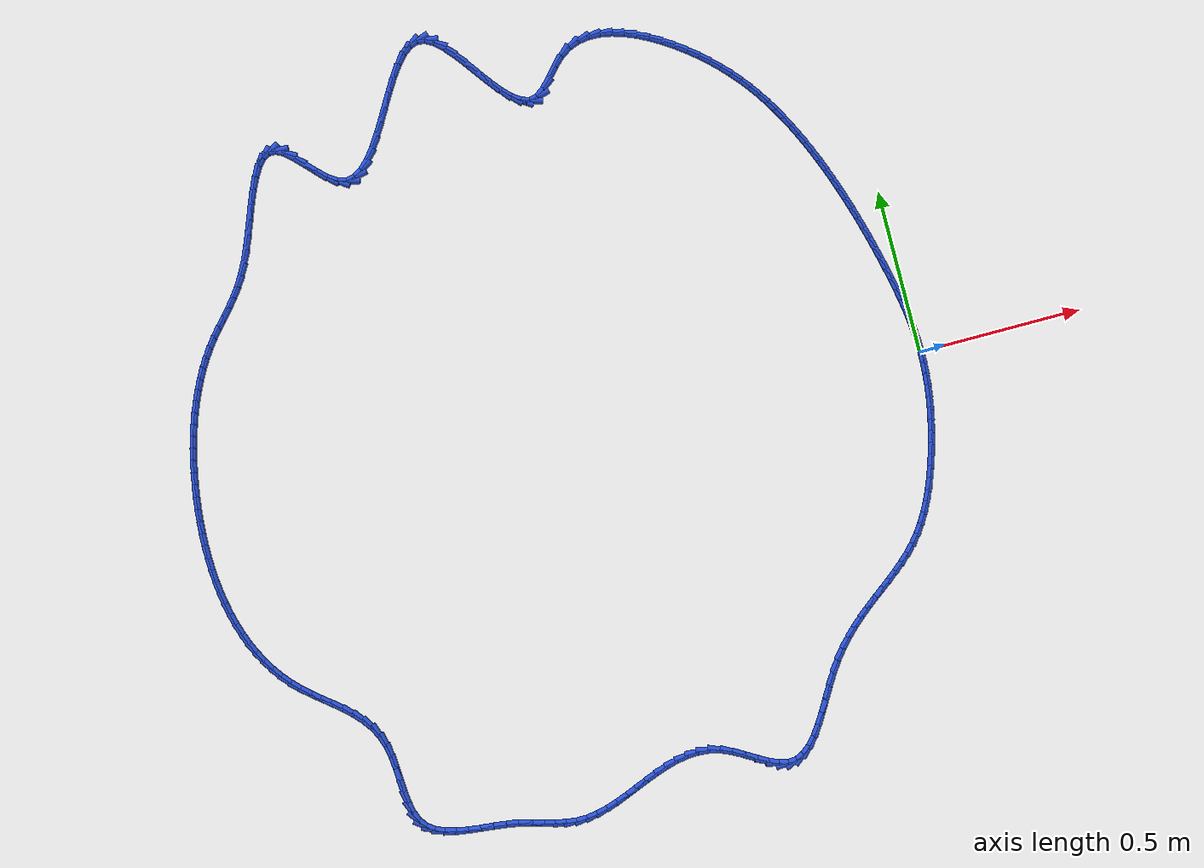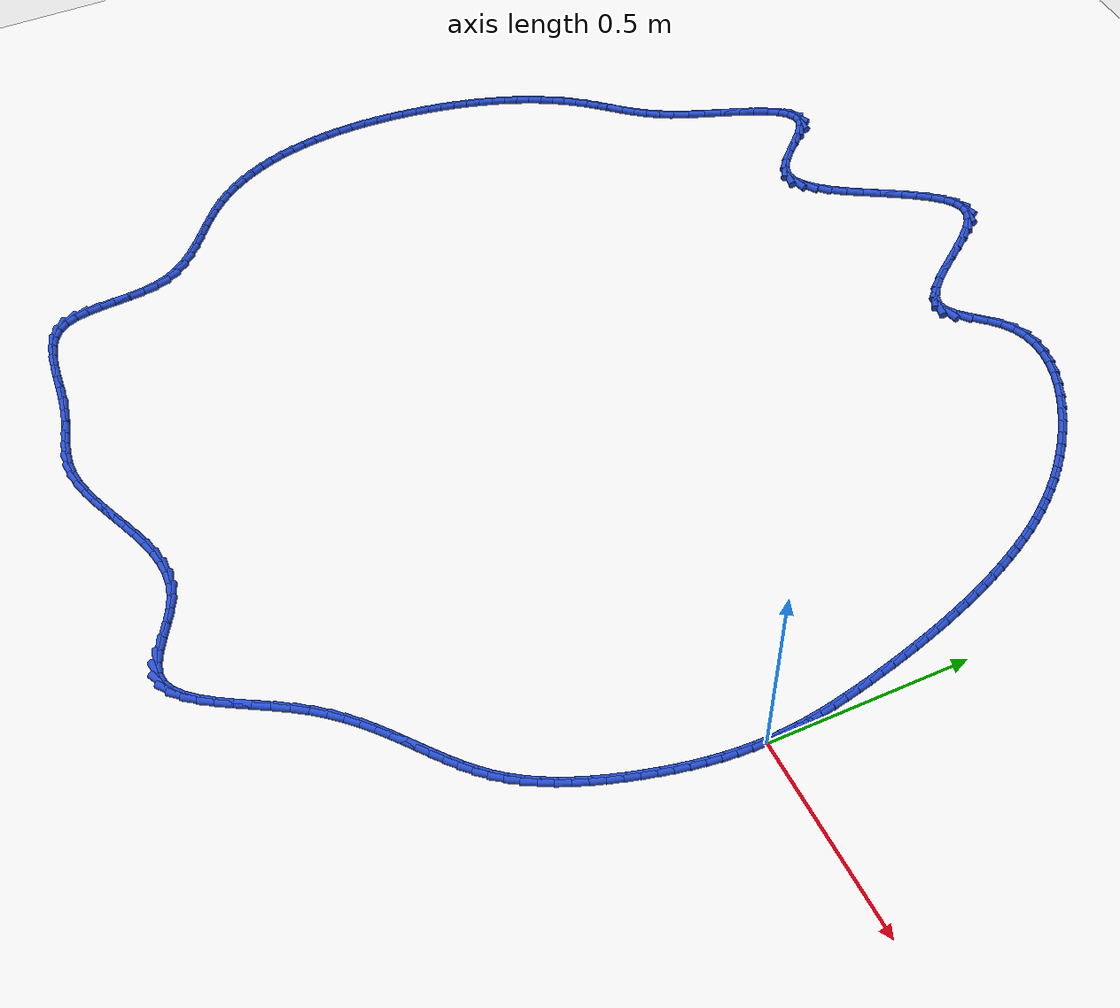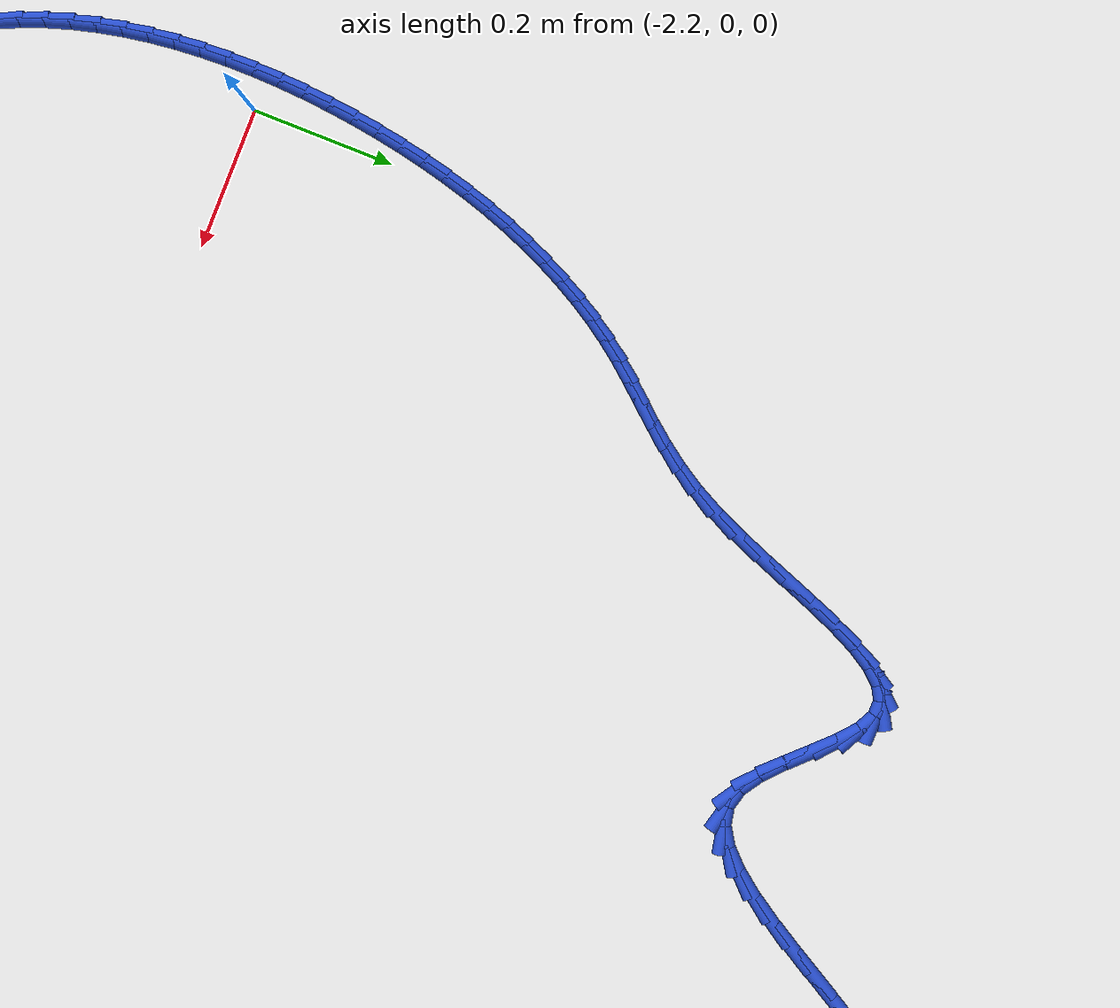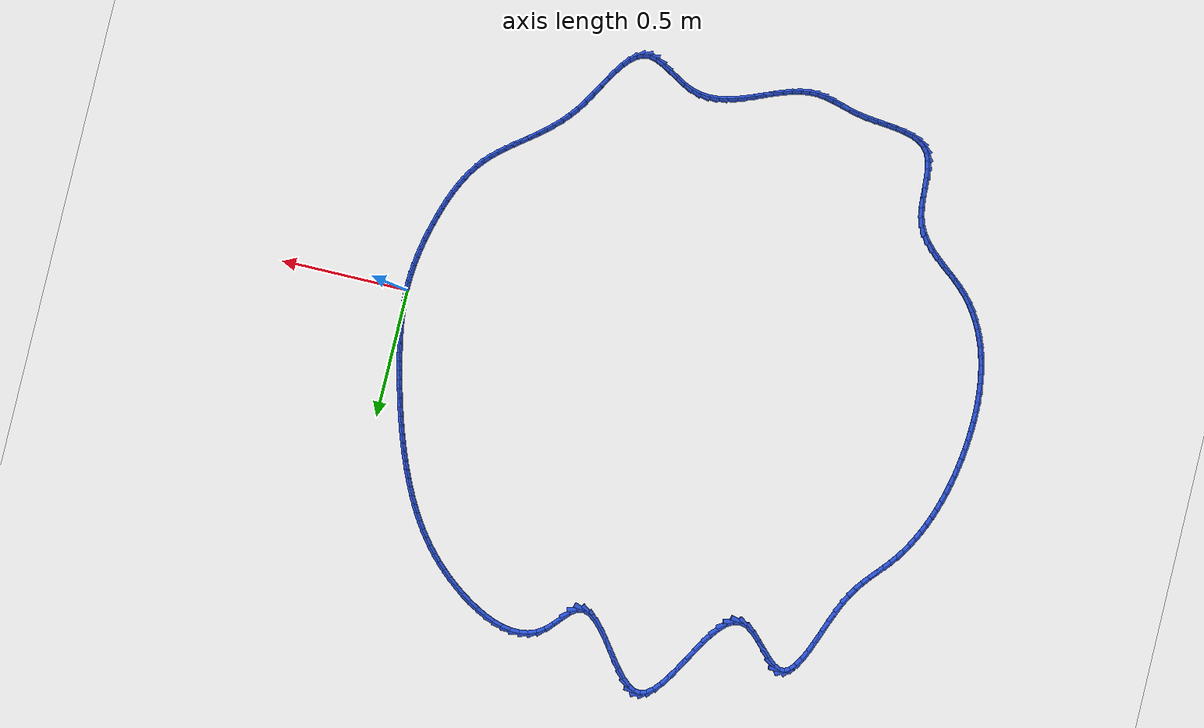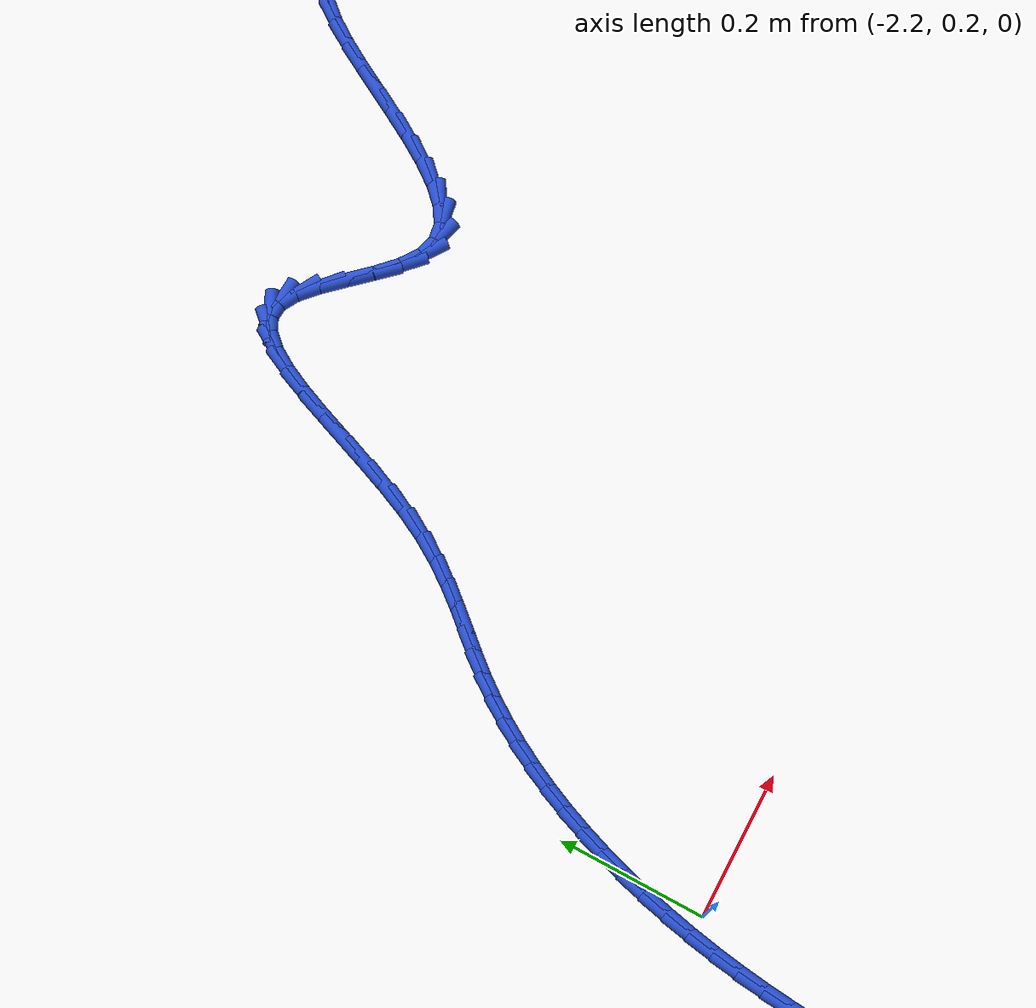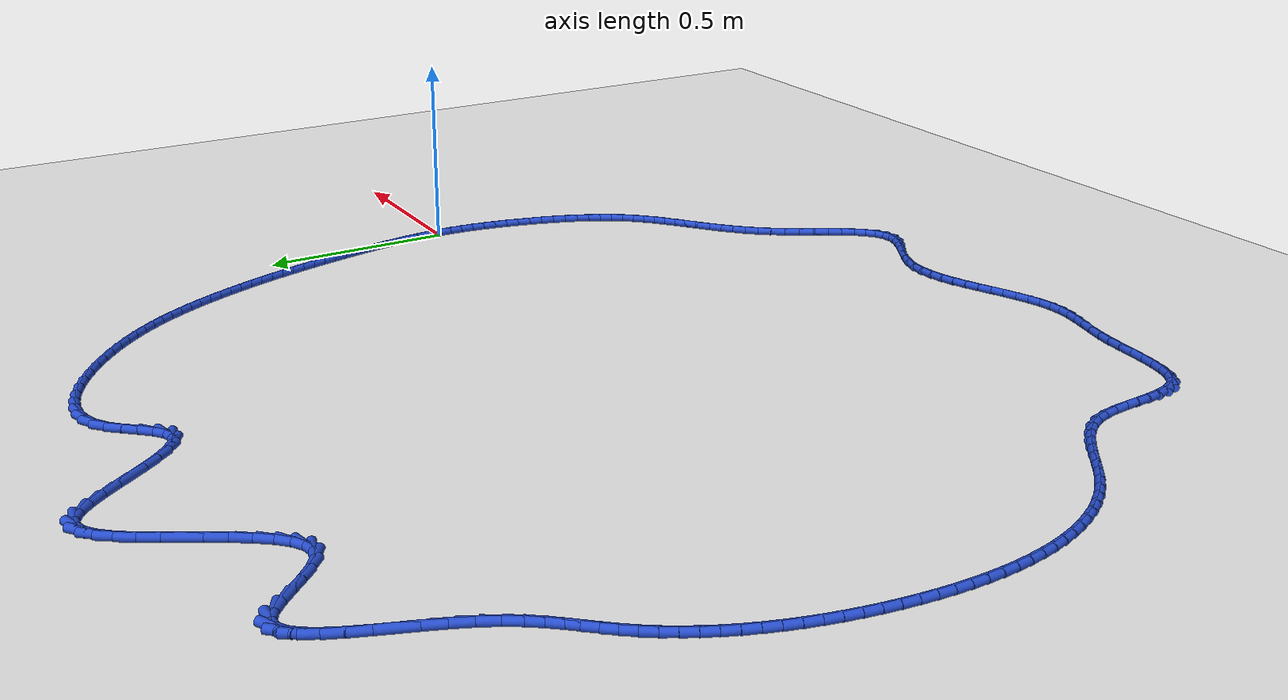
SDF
<sdf version="1.6">
 <world name="default">
  <light name="sun" type="directional">
   <pose>0 0 10 0 -0 0</pose>
   <diffuse>0.8 0.8 0.8 1</diffuse>
   <specular>0.2 0.2 0.2 1</specular>
   <attenuation>
    <range>1000</range>
    <constant>0.9</constant>
    <linear>0.01</linear>
    <quadratic>0.001</quadratic>
   </attenuation>
   <direction>-0.5 0.1 -0.9</direction>
  </light>
  <model name="ground_plane">
   <static>1</static>
   <link name="link">
    <collision name="collision">
     <geometry><plane><normal>0 0 1</normal><size>100 100</size></plane></geometry>
     <surface><friction><ode><mu>100</mu><mu2>50</mu2></ode></friction></surface>
    </collision>
    <visual name="visual">
     <cast_shadows>0</cast_shadows>
     <geometry><plane><normal>0 0 1</normal><size>100 100</size></plane></geometry>
     <material>
      <script><uri>file://media/materials/scripts/gazebo.material</uri><name>Gazebo/WhiteGlow</name></script>
     </material>
    </visual>
   </link>
  </model>
  <gravity>0 0 -9.8</gravity>
  <magnetic_field>6e-06 2.3e-05 -4.2e-05</magnetic_field>
  <atmosphere type="adiabatic"/>
  <physics name="default_physics" default="0" type="ode">
   <max_step_size>0.001</max_step_size>
   <real_time_factor>1</real_time_factor>
   <real_time_update_rate>1000</real_time_update_rate>
  </physics>
  <scene><ambient>0.4 0.4 0.4 1</ambient><background>0.7 0.7 0.7 1</background><shadows>1</shadows></scene>
  <spherical_coordinates>
   <surface_model>EARTH_WGS84</surface_model>
   <latitude_deg>0</latitude_deg>
   <longitude_deg>0</longitude_deg>
   <elevation>0</elevation>
   <heading_deg>0</heading_deg>
  </spherical_coordinates>
  <model name="line">
   <link name="link_0">
    <pose>3.469446951953614e-18 -4.85722573273506e-17 0.01 0 1.57 -1.5387059002571244</pose>
    <collision name="collision">
     <geometry><cylinder><radius>0.01</radius><length>0.08</length></cylinder></geometry>
    </collision>
    <visual name="visual">
     <material>
      <script><name>Gazebo/Blue</name><uri>file://media/materials/scripts/gazebo.material</uri></script>
     </material>
     <geometry><cylinder><radius>0.01</radius><length>0.08</length></cylinder></geometry>
    </visual>
   </link>
   <link name="link_1">
    <pose>-0.001106931188184582 0.03448228367683688 0.01 0 1.57 -1.4994186272707228</pose>
    <collision name="collision">
     <geometry><cylinder><radius>0.01</radius><length>0.08</length></cylinder></geometry>
    </collision>
    <visual name="visual">
     <material>
      <script><name>Gazebo/Blue</name><uri>file://media/materials/scripts/gazebo.material</uri></script>
     </material>
     <geometry><cylinder><radius>0.01</radius><length>0.08</length></cylinder></geometry>
    </visual>
   </link>
   <link name="link_2">
    <pose>-0.003572972429707237 0.06897277382835876 0.01 0 1.57 -1.4643418091511784</pose>
    <collision name="collision">
     <geometry><cylinder><radius>0.01</radius><length>0.08</length></cylinder></geometry>
    </collision>
    <visual name="visual">
     <material>
      <script><name>Gazebo/Blue</name><uri>file://media/materials/scripts/gazebo.material</uri></script>
     </material>
     <geometry><cylinder><radius>0.01</radius><length>0.08</length></cylinder></geometry>
    </visual>
   </link>
   <link name="link_3">
    <pose>-0.007258569617800207 0.1034632239956365 0.01 0 1.57 -1.4334615511302427</pose>
    <collision name="collision">
     <geometry><cylinder><radius>0.01</radius><length>0.08</length></cylinder></geometry>
    </collision>
    <visual name="visual">
     <material>
      <script><name>Gazebo/Blue</name><uri>file://media/materials/scripts/gazebo.material</uri></script>
     </material>
     <geometry><cylinder><radius>0.01</radius><length>0.08</length></cylinder></geometry>
    </visual>
   </link>
   <link name="link_4">
    <pose>-0.012024168645695749 0.13794538771974094 0.01 0 1.57 -1.4067269451403537</pose>
    <collision name="collision">
     <geometry><cylinder><radius>0.01</radius><length>0.08</length></cylinder></geometry>
    </collision>
    <visual name="visual">
     <material>
      <script><name>Gazebo/Blue</name><uri>file://media/materials/scripts/gazebo.material</uri></script>
     </material>
     <geometry><cylinder><radius>0.01</radius><length>0.08</length></cylinder></geometry>
    </visual>
   </link>
   <link name="link_5">
    <pose>-0.017730215406626105 0.17241101854174293 0.01 0 1.57 -1.3840664514117882</pose>
    <collision name="collision">
     <geometry><cylinder><radius>0.01</radius><length>0.08</length></cylinder></geometry>
    </collision>
    <visual name="visual">
     <material>
      <script><name>Gazebo/Blue</name><uri>file://media/materials/scripts/gazebo.material</uri></script>
     </material>
     <geometry><cylinder><radius>0.01</radius><length>0.08</length></cylinder></geometry>
    </visual>
   </link>
   <link name="link_6">
    <pose>-0.024237155793823534 0.20685187000271332 0.01 0 1.57 -1.3654014139635433</pose>
    <collision name="collision">
     <geometry><cylinder><radius>0.01</radius><length>0.08</length></cylinder></geometry>
    </collision>
    <visual name="visual">
     <material>
      <script><name>Gazebo/Blue</name><uri>file://media/materials/scripts/gazebo.material</uri></script>
     </material>
     <geometry><cylinder><radius>0.01</radius><length>0.08</length></cylinder></geometry>
    </visual>
   </link>
   <link name="link_7">
    <pose>-0.03140543570052029 0.24125969564372302 0.01 0 1.57 -1.3506567571870371</pose>
    <collision name="collision">
     <geometry><cylinder><radius>0.01</radius><length>0.08</length></cylinder></geometry>
    </collision>
    <visual name="visual">
     <material>
      <script><name>Gazebo/Blue</name><uri>file://media/materials/scripts/gazebo.material</uri></script>
     </material>
     <geometry><cylinder><radius>0.01</radius><length>0.08</length></cylinder></geometry>
    </visual>
   </link>
   <link name="link_8">
    <pose>-0.039095501019948624 0.2756262490058428 0.01 0 1.57 -1.33934520246429</pose>
    <collision name="collision">
     <geometry><cylinder><radius>0.01</radius><length>0.08</length></cylinder></geometry>
    </collision>
    <visual name="visual">
     <material>
      <script><name>Gazebo/Blue</name><uri>file://media/materials/scripts/gazebo.material</uri></script>
     </material>
     <geometry><cylinder><radius>0.01</radius><length>0.08</length></cylinder></geometry>
    </visual>
   </link>
   <link name="link_9">
    <pose>-0.04718261433602917 0.3099409973067222 0.01 0 1.57 -1.328505576449126</pose>
    <collision name="collision">
     <geometry><cylinder><radius>0.01</radius><length>0.08</length></cylinder></geometry>
    </collision>
    <visual name="visual">
     <material>
      <script><name>Gazebo/Blue</name><uri>file://media/materials/scripts/gazebo.material</uri></script>
     </material>
     <geometry><cylinder><radius>0.01</radius><length>0.08</length></cylinder></geometry>
    </visual>
   </link>
   <link name="link_10">
    <pose>-0.05564406958337792 0.3441776635825525 0.01 0 1.57 -1.3168845990055629</pose>
    <collision name="collision">
     <geometry><cylinder><radius>0.01</radius><length>0.08</length></cylinder></geometry>
    </collision>
    <visual name="visual">
     <material>
      <script><name>Gazebo/Blue</name><uri>file://media/materials/scripts/gazebo.material</uri></script>
     </material>
     <geometry><cylinder><radius>0.01</radius><length>0.08</length></cylinder></geometry>
    </visual>
   </link>
   <link name="link_11">
    <pose>-0.0645001225209716 0.37830334154673434 0.01 0 1.57 -1.3044537958714792</pose>
    <collision name="collision">
     <geometry><cylinder><radius>0.01</radius><length>0.08</length></cylinder></geometry>
    </collision>
    <visual name="visual">
     <material>
      <script><name>Gazebo/Blue</name><uri>file://media/materials/scripts/gazebo.material</uri></script>
     </material>
     <geometry><cylinder><radius>0.01</radius><length>0.08</length></cylinder></geometry>
    </visual>
   </link>
   <link name="link_12">
    <pose>-0.07377117882215029 0.41228510177978905 0.01 0 1.57 -1.2911866325705592</pose>
    <collision name="collision">
     <geometry><cylinder><radius>0.01</radius><length>0.08</length></cylinder></geometry>
    </collision>
    <visual name="visual">
     <material>
      <script><name>Gazebo/Blue</name><uri>file://media/materials/scripts/gazebo.material</uri></script>
     </material>
     <geometry><cylinder><radius>0.01</radius><length>0.08</length></cylinder></geometry>
    </visual>
   </link>
   <link name="link_13">
    <pose>-0.083477644160254 0.44609001486223776 0.01 0 1.57 -1.2770543189389454</pose>
    <collision name="collision">
     <geometry><cylinder><radius>0.01</radius><length>0.08</length></cylinder></geometry>
    </collision>
    <visual name="visual">
     <material>
      <script><name>Gazebo/Blue</name><uri>file://media/materials/scripts/gazebo.material</uri></script>
     </material>
     <geometry><cylinder><radius>0.01</radius><length>0.08</length></cylinder></geometry>
    </visual>
   </link>
   <link name="link_14">
    <pose>-0.09363992420862281 0.47968515137460177 0.01 0 1.57 -1.2620259272889152</pose>
    <collision name="collision">
     <geometry><cylinder><radius>0.01</radius><length>0.08</length></cylinder></geometry>
    </collision>
    <visual name="visual">
     <material>
      <script><name>Gazebo/Blue</name><uri>file://media/materials/scripts/gazebo.material</uri></script>
     </material>
     <geometry><cylinder><radius>0.01</radius><length>0.08</length></cylinder></geometry>
    </visual>
   </link>
   <link name="link_15">
    <pose>-0.10427842464059679 0.5130375818974023 0.01 0 1.57 -1.2460685435818915</pose>
    <collision name="collision">
     <geometry><cylinder><radius>0.01</radius><length>0.08</length></cylinder></geometry>
    </collision>
    <visual name="visual">
     <material>
      <script><name>Gazebo/Blue</name><uri>file://media/materials/scripts/gazebo.material</uri></script>
     </material>
     <geometry><cylinder><radius>0.01</radius><length>0.08</length></cylinder></geometry>
    </visual>
   </link>
   <link name="link_16">
    <pose>-0.11541355112951603 0.5461143770111606 0.01 0 1.57 -1.2291474615913758</pose>
    <collision name="collision">
     <geometry><cylinder><radius>0.01</radius><length>0.08</length></cylinder></geometry>
    </collision>
    <visual name="visual">
     <material>
      <script><name>Gazebo/Blue</name><uri>file://media/materials/scripts/gazebo.material</uri></script>
     </material>
     <geometry><cylinder><radius>0.01</radius><length>0.08</length></cylinder></geometry>
    </visual>
   </link>
   <link name="link_17">
    <pose>-0.12706570934872058 0.578882607296398 0.01 0 1.57 -1.2112264312979661</pose>
    <collision name="collision">
     <geometry><cylinder><radius>0.01</radius><length>0.08</length></cylinder></geometry>
    </collision>
    <visual name="visual">
     <material>
      <script><name>Gazebo/Blue</name><uri>file://media/materials/scripts/gazebo.material</uri></script>
     </material>
     <geometry><cylinder><radius>0.01</radius><length>0.08</length></cylinder></geometry>
    </visual>
   </link>
   <link name="link_18">
    <pose>-0.13925530497155042 0.6113093433336356 0.01 0 1.57 -1.1922679740397317</pose>
    <collision name="collision">
     <geometry><cylinder><radius>0.01</radius><length>0.08</length></cylinder></geometry>
    </collision>
    <visual name="visual">
     <material>
      <script><name>Gazebo/Blue</name><uri>file://media/materials/scripts/gazebo.material</uri></script>
     </material>
     <geometry><cylinder><radius>0.01</radius><length>0.08</length></cylinder></geometry>
    </visual>
   </link>
   <link name="link_19">
    <pose>-0.15200274367134567 0.6433616557033945 0.01 0 1.57 -1.1722337781413403</pose>
    <collision name="collision">
     <geometry><cylinder><radius>0.01</radius><length>0.08</length></cylinder></geometry>
    </collision>
    <visual name="visual">
     <material>
      <script><name>Gazebo/Blue</name><uri>file://media/materials/scripts/gazebo.material</uri></script>
     </material>
     <geometry><cylinder><radius>0.01</radius><length>0.08</length></cylinder></geometry>
    </visual>
   </link>
   <link name="link_20">
    <pose>-0.16532843112144646 0.6750066149861964 0.01 0 1.57 -1.1510851897197338</pose>
    <collision name="collision">
     <geometry><cylinder><radius>0.01</radius><length>0.08</length></cylinder></geometry>
    </collision>
    <visual name="visual">
     <material>
      <script><name>Gazebo/Blue</name><uri>file://media/materials/scripts/gazebo.material</uri></script>
     </material>
     <geometry><cylinder><radius>0.01</radius><length>0.08</length></cylinder></geometry>
    </visual>
   </link>
   <link name="link_21">
    <pose>-0.1792527729951927 0.7062112917625619 0.01 0 1.57 -1.1286717989246011</pose>
    <collision name="collision">
     <geometry><cylinder><radius>0.01</radius><length>0.08</length></cylinder></geometry>
    </collision>
    <visual name="visual">
     <material>
      <script><name>Gazebo/Blue</name><uri>file://media/materials/scripts/gazebo.material</uri></script>
     </material>
     <geometry><cylinder><radius>0.01</radius><length>0.08</length></cylinder></geometry>
    </visual>
   </link>
   <link name="link_22">
    <pose>-0.19380096820769038 0.7369439811848413 0.01 0 1.57 -1.103786442105796</pose>
    <collision name="collision">
     <geometry><cylinder><radius>0.01</radius><length>0.08</length></cylinder></geometry>
    </collision>
    <visual name="visual">
     <material>
      <script><name>Gazebo/Blue</name><uri>file://media/materials/scripts/gazebo.material</uri></script>
     </material>
     <geometry><cylinder><radius>0.01</radius><length>0.08</length></cylinder></geometry>
    </visual>
   </link>
   <link name="link_23">
    <pose>-0.2090493108435047 0.7671860321398195 0.01 0 1.57 -1.0757743835521465</pose>
    <collision name="collision">
     <geometry><cylinder><radius>0.01</radius><length>0.08</length></cylinder></geometry>
    </collision>
    <visual name="visual">
     <material>
      <script><name>Gazebo/Blue</name><uri>file://media/materials/scripts/gazebo.material</uri></script>
     </material>
     <geometry><cylinder><radius>0.01</radius><length>0.08</length></cylinder></geometry>
    </visual>
   </link>
   <link name="link_24">
    <pose>-0.22510498805990636 0.7969266860405463 0.01 0 1.57 -1.0447509270802702</pose>
    <collision name="collision">
     <geometry><cylinder><radius>0.01</radius><length>0.08</length></cylinder></geometry>
    </collision>
    <visual name="visual">
     <material>
      <script><name>Gazebo/Blue</name><uri>file://media/materials/scripts/gazebo.material</uri></script>
     </material>
     <geometry><cylinder><radius>0.01</radius><length>0.08</length></cylinder></geometry>
    </visual>
   </link>
   <link name="link_25">
    <pose>-0.24207561634802352 0.8261552939857869 0.01 0 1.57 -1.0108954349804724</pose>
    <collision name="collision">
     <geometry><cylinder><radius>0.01</radius><length>0.08</length></cylinder></geometry>
    </collision>
    <visual name="visual">
     <material>
      <script><name>Gazebo/Blue</name><uri>file://media/materials/scripts/gazebo.material</uri></script>
     </material>
     <geometry><cylinder><radius>0.01</radius><length>0.08</length></cylinder></geometry>
    </visual>
   </link>
   <link name="link_26">
    <pose>-0.2600688121989844 0.8548612070743049 0.01 0 1.57 -0.9744445872556786</pose>
    <collision name="collision">
     <geometry><cylinder><radius>0.01</radius><length>0.08</length></cylinder></geometry>
    </collision>
    <visual name="visual">
     <material>
      <script><name>Gazebo/Blue</name><uri>file://media/materials/scripts/gazebo.material</uri></script>
     </material>
     <geometry><cylinder><radius>0.01</radius><length>0.08</length></cylinder></geometry>
    </visual>
   </link>
   <link name="link_27">
    <pose>-0.27919219210391727 0.8830337764048655 0.01 0 1.57 -0.935692609687109</pose>
    <collision name="collision">
     <geometry><cylinder><radius>0.01</radius><length>0.08</length></cylinder></geometry>
    </collision>
    <visual name="visual">
     <material>
      <script><name>Gazebo/Blue</name><uri>file://media/materials/scripts/gazebo.material</uri></script>
     </material>
     <geometry><cylinder><radius>0.01</radius><length>0.08</length></cylinder></geometry>
    </visual>
   </link>
   <link name="link_28">
    <pose>-0.29955337255395004 0.9106623530762327 0.01 0 1.57 -0.8949876478548601</pose>
    <collision name="collision">
     <geometry><cylinder><radius>0.01</radius><length>0.08</length></cylinder></geometry>
    </collision>
    <visual name="visual">
     <material>
      <script><name>Gazebo/Blue</name><uri>file://media/materials/scripts/gazebo.material</uri></script>
     </material>
     <geometry><cylinder><radius>0.01</radius><length>0.08</length></cylinder></geometry>
    </visual>
   </link>
   <link name="link_29">
    <pose>-0.3212599700402111 0.9377362881871713 0.01 0 1.57 -0.8527238754158645</pose>
    <collision name="collision">
     <geometry><cylinder><radius>0.01</radius><length>0.08</length></cylinder></geometry>
    </collision>
    <visual name="visual">
     <material>
      <script><name>Gazebo/Blue</name><uri>file://media/materials/scripts/gazebo.material</uri></script>
     </material>
     <geometry><cylinder><radius>0.01</radius><length>0.08</length></cylinder></geometry>
    </visual>
   </link>
   <link name="link_30">
    <pose>-0.3444196010538286 0.9642449328364454 0.01 0 1.57 -0.8093294827232611</pose>
    <collision name="collision">
     <geometry><cylinder><radius>0.01</radius><length>0.08</length></cylinder></geometry>
    </collision>
    <visual name="visual">
     <material>
      <script><name>Gazebo/Blue</name><uri>file://media/materials/scripts/gazebo.material</uri></script>
     </material>
     <geometry><cylinder><radius>0.01</radius><length>0.08</length></cylinder></geometry>
    </visual>
   </link>
   <link name="link_31">
    <pose>-0.36913988208593057 0.9901776381228198 0.01 0 1.57 -0.7652513336959319</pose>
    <collision name="collision">
     <geometry><cylinder><radius>0.01</radius><length>0.08</length></cylinder></geometry>
    </collision>
    <visual name="visual">
     <material>
      <script><name>Gazebo/Blue</name><uri>file://media/materials/scripts/gazebo.material</uri></script>
     </material>
     <geometry><cylinder><radius>0.01</radius><length>0.08</length></cylinder></geometry>
    </visual>
   </link>
   <link name="link_32">
    <pose>-0.39552842962764534 1.0155237551450589 0.01 0 1.57 -0.7209376593597855</pose>
    <collision name="collision">
     <geometry><cylinder><radius>0.01</radius><length>0.08</length></cylinder></geometry>
    </collision>
    <visual name="visual">
     <material>
      <script><name>Gazebo/Blue</name><uri>file://media/materials/scripts/gazebo.material</uri></script>
     </material>
     <geometry><cylinder><radius>0.01</radius><length>0.08</length></cylinder></geometry>
    </visual>
   </link>
   <link name="link_33">
    <pose>-0.423692860170101 1.040272635001927 0.01 0 1.57 -0.6768205229973143</pose>
    <collision name="collision">
     <geometry><cylinder><radius>0.01</radius><length>0.08</length></cylinder></geometry>
    </collision>
    <visual name="visual">
     <material>
      <script><name>Gazebo/Blue</name><uri>file://media/materials/scripts/gazebo.material</uri></script>
     </material>
     <geometry><cylinder><radius>0.01</radius><length>0.08</length></cylinder></geometry>
    </visual>
   </link>
   <link name="link_34">
    <pose>-0.45374079020442576 1.064413628792189 0.01 0 1.57 -0.6328383945299714</pose>
    <collision name="collision">
     <geometry><cylinder><radius>0.01</radius><length>0.08</length></cylinder></geometry>
    </collision>
    <visual name="visual">
     <material>
      <script><name>Gazebo/Blue</name><uri>file://media/materials/scripts/gazebo.material</uri></script>
     </material>
     <geometry><cylinder><radius>0.01</radius><length>0.08</length></cylinder></geometry>
    </visual>
   </link>
   <link name="link_35">
    <pose>-0.4857378928849913 1.0878825777732137 0.01 0 1.57 -0.5850253377321937</pose>
    <collision name="collision">
     <geometry><cylinder><radius>0.01</radius><length>0.08</length></cylinder></geometry>
    </collision>
    <visual name="visual">
     <material>
      <script><name>Gazebo/Blue</name><uri>file://media/materials/scripts/gazebo.material</uri></script>
     </material>
     <geometry><cylinder><radius>0.01</radius><length>0.08</length></cylinder></geometry>
    </visual>
   </link>
   <link name="link_36">
    <pose>-0.5194171135733677 1.1101908407267875 0.01 0 1.57 -0.5297281601589839</pose>
    <collision name="collision">
     <geometry><cylinder><radius>0.01</radius><length>0.08</length></cylinder></geometry>
    </collision>
    <visual name="visual">
     <material>
      <script><name>Gazebo/Blue</name><uri>file://media/materials/scripts/gazebo.material</uri></script>
     </material>
     <geometry><cylinder><radius>0.01</radius><length>0.08</length></cylinder></geometry>
    </visual>
   </link>
   <link name="link_37">
    <pose>-0.554352880361563 1.1306475456488643 0.01 0 1.57 -0.4643217695408438</pose>
    <collision name="collision">
     <geometry><cylinder><radius>0.01</radius><length>0.08</length></cylinder></geometry>
    </collision>
    <visual name="visual">
     <material>
      <script><name>Gazebo/Blue</name><uri>file://media/materials/scripts/gazebo.material</uri></script>
     </material>
     <geometry><cylinder><radius>0.01</radius><length>0.08</length></cylinder></geometry>
    </visual>
   </link>
   <link name="link_38">
    <pose>-0.5901186488928541 1.1485605799193341 0.01 0 1.57 -0.38549111227731736</pose>
    <collision name="collision">
     <geometry><cylinder><radius>0.01</radius><length>0.08</length></cylinder></geometry>
    </collision>
    <visual name="visual">
     <material>
      <script><name>Gazebo/Blue</name><uri>file://media/materials/scripts/gazebo.material</uri></script>
     </material>
     <geometry><cylinder><radius>0.01</radius><length>0.08</length></cylinder></geometry>
    </visual>
   </link>
   <link name="link_39">
    <pose>-0.6262878748105175 1.1632378309180864 0.01 0 1.57 -0.2890568928570356</pose>
    <collision name="collision">
     <geometry><cylinder><radius>0.01</radius><length>0.08</length></cylinder></geometry>
    </collision>
    <visual name="visual">
     <material>
      <script><name>Gazebo/Blue</name><uri>file://media/materials/scripts/gazebo.material</uri></script>
     </material>
     <geometry><cylinder><radius>0.01</radius><length>0.08</length></cylinder></geometry>
    </visual>
   </link>
   <link name="link_40">
    <pose>-0.66243401375783 1.173987186025011 0.01 0 1.57 -0.17004891429307034</pose>
    <collision name="collision">
     <geometry><cylinder><radius>0.01</radius><length>0.08</length></cylinder></geometry>
    </collision>
    <visual name="visual">
     <material>
      <script><name>Gazebo/Blue</name><uri>file://media/materials/scripts/gazebo.material</uri></script>
     </material>
     <geometry><cylinder><radius>0.01</radius><length>0.08</length></cylinder></geometry>
    </visual>
   </link>
   <link name="link_41">
    <pose>-0.6981305213780676 1.1801165326199978 0.01 0 1.57 -0.02346547020581845</pose>
    <collision name="collision">
     <geometry><cylinder><radius>0.01</radius><length>0.08</length></cylinder></geometry>
    </collision>
    <visual name="visual">
     <material>
      <script><name>Gazebo/Blue</name><uri>file://media/materials/scripts/gazebo.material</uri></script>
     </material>
     <geometry><cylinder><radius>0.01</radius><length>0.08</length></cylinder></geometry>
    </visual>
   </link>
   <link name="link_42">
    <pose>-0.732950853314508 1.1809337580829358 0.01 0 1.57 0.15353675549089574</pose>
    <collision name="collision">
     <geometry><cylinder><radius>0.01</radius><length>0.08</length></cylinder></geometry>
    </collision>
    <visual name="visual">
     <material>
      <script><name>Gazebo/Blue</name><uri>file://media/materials/scripts/gazebo.material</uri></script>
     </material>
     <geometry><cylinder><radius>0.01</radius><length>0.08</length></cylinder></geometry>
    </visual>
   </link>
   <link name="link_43">
    <pose>-0.7664684652104277 1.175746749793715 0.01 0 1.57 0.3577422237787321</pose>
    <collision name="collision">
     <geometry><cylinder><radius>0.01</radius><length>0.08</length></cylinder></geometry>
    </collision>
    <visual name="visual">
     <material>
      <script><name>Gazebo/Blue</name><uri>file://media/materials/scripts/gazebo.material</uri></script>
     </material>
     <geometry><cylinder><radius>0.01</radius><length>0.08</length></cylinder></geometry>
    </visual>
   </link>
   <link name="link_44">
    <pose>-0.798256812709103 1.1638633951322253 0.01 0 1.57 0.5766273810100219</pose>
    <collision name="collision">
     <geometry><cylinder><radius>0.01</radius><length>0.08</length></cylinder></geometry>
    </collision>
    <visual name="visual">
     <material>
      <script><name>Gazebo/Blue</name><uri>file://media/materials/scripts/gazebo.material</uri></script>
     </material>
     <geometry><cylinder><radius>0.01</radius><length>0.08</length></cylinder></geometry>
    </visual>
   </link>
   <link name="link_45">
    <pose>-0.8278893572024018 1.144591610328662 0.01 0 1.57 0.7667213764128141</pose>
    <collision name="collision">
     <geometry><cylinder><radius>0.01</radius><length>0.08</length></cylinder></geometry>
    </collision>
    <visual name="visual">
     <material>
      <script><name>Gazebo/Blue</name><uri>file://media/materials/scripts/gazebo.material</uri></script>
     </material>
     <geometry><cylinder><radius>0.01</radius><length>0.08</length></cylinder></geometry>
    </visual>
   </link>
   <link name="link_46">
    <pose>-0.8551558932639086 1.1183250173844301 0.01 0 1.57 0.8483430362697949</pose>
    <collision name="collision">
     <geometry><cylinder><radius>0.01</radius><length>0.08</length></cylinder></geometry>
    </collision>
    <visual name="visual">
     <material>
      <script><name>Gazebo/Blue</name><uri>file://media/materials/scripts/gazebo.material</uri></script>
     </material>
     <geometry><cylinder><radius>0.01</radius><length>0.08</length></cylinder></geometry>
    </visual>
   </link>
   <link name="link_47">
    <pose>-0.8806353522398481 1.0894176587113753 0.01 0 1.57 0.8216456822103181</pose>
    <collision name="collision">
     <geometry><cylinder><radius>0.01</radius><length>0.08</length></cylinder></geometry>
    </collision>
    <visual name="visual">
     <material>
      <script><name>Gazebo/Blue</name><uri>file://media/materials/scripts/gazebo.material</uri></script>
     </material>
     <geometry><cylinder><radius>0.01</radius><length>0.08</length></cylinder></geometry>
    </visual>
   </link>
   <link name="link_48">
    <pose>-0.9050865511566233 1.0631263643546527 0.01 0 1.57 0.650925079657704</pose>
    <collision name="collision">
     <geometry><cylinder><radius>0.01</radius><length>0.08</length></cylinder></geometry>
    </collision>
    <visual name="visual">
     <material>
      <script><name>Gazebo/Blue</name><uri>file://media/materials/scripts/gazebo.material</uri></script>
     </material>
     <geometry><cylinder><radius>0.01</radius><length>0.08</length></cylinder></geometry>
    </visual>
   </link>
   <link name="link_49">
    <pose>-0.929268307040638 1.0447079643594201 0.01 0 1.57 0.22738726000629253</pose>
    <collision name="collision">
     <geometry><cylinder><radius>0.01</radius><length>0.08</length></cylinder></geometry>
    </collision>
    <visual name="visual">
     <material>
      <script><name>Gazebo/Blue</name><uri>file://media/materials/scripts/gazebo.material</uri></script>
     </material>
     <geometry><cylinder><radius>0.01</radius><length>0.08</length></cylinder></geometry>
    </visual>
   </link>
   <link name="link_50">
    <pose>-0.9538927391358144 1.0390101401021683 0.01 0 1.57 -0.28409257812150845</pose>
    <collision name="collision">
     <geometry><cylinder><radius>0.01</radius><length>0.08</length></cylinder></geometry>
    </collision>
    <visual name="visual">
     <material>
      <script><name>Gazebo/Blue</name><uri>file://media/materials/scripts/gazebo.material</uri></script>
     </material>
     <geometry><cylinder><radius>0.01</radius><length>0.08</length></cylinder></geometry>
    </visual>
   </link>
   <link name="link_51">
    <pose>-0.9791591771869583 1.0463877013556677 0.01 0 1.57 -0.6101024004403374</pose>
    <collision name="collision">
     <geometry><cylinder><radius>0.01</radius><length>0.08</length></cylinder></geometry>
    </collision>
    <visual name="visual">
     <material>
      <script><name>Gazebo/Blue</name><uri>file://media/materials/scripts/gazebo.material</uri></script>
     </material>
     <geometry><cylinder><radius>0.01</radius><length>0.08</length></cylinder></geometry>
    </visual>
   </link>
   <link name="link_52">
    <pose>-1.004949860349779 1.0644172276324797 0.01 0 1.57 -0.7858641204738551</pose>
    <collision name="collision">
     <geometry><cylinder><radius>0.01</radius><length>0.08</length></cylinder></geometry>
    </collision>
    <visual name="visual">
     <material>
      <script><name>Gazebo/Blue</name><uri>file://media/materials/scripts/gazebo.material</uri></script>
     </material>
     <geometry><cylinder><radius>0.01</radius><length>0.08</length></cylinder></geometry>
    </visual>
   </link>
   <link name="link_53">
    <pose>-1.0311423273660987 1.0906341151601864 0.01 0 1.57 -0.8787355006214235</pose>
    <collision name="collision">
     <geometry><cylinder><radius>0.01</radius><length>0.08</length></cylinder></geometry>
    </collision>
    <visual name="visual">
     <material>
      <script><name>Gazebo/Blue</name><uri>file://media/materials/scripts/gazebo.material</uri></script>
     </material>
     <geometry><cylinder><radius>0.01</radius><length>0.08</length></cylinder></geometry>
    </visual>
   </link>
   <link name="link_54">
    <pose>-1.0576141169777407 1.1225737601663701 0.01 0 1.57 -0.9231207834619701</pose>
    <collision name="collision">
     <geometry><cylinder><radius>0.01</radius><length>0.08</length></cylinder></geometry>
    </collision>
    <visual name="visual">
     <material>
      <script><name>Gazebo/Blue</name><uri>file://media/materials/scripts/gazebo.material</uri></script>
     </material>
     <geometry><cylinder><radius>0.01</radius><length>0.08</length></cylinder></geometry>
    </visual>
   </link>
   <link name="link_55">
    <pose>-1.0842427679265265 1.1577715588786133 0.01 0 1.57 -0.9331974266913816</pose>
    <collision name="collision">
     <geometry><cylinder><radius>0.01</radius><length>0.08</length></cylinder></geometry>
    </collision>
    <visual name="visual">
     <material>
      <script><name>Gazebo/Blue</name><uri>file://media/materials/scripts/gazebo.material</uri></script>
     </material>
     <geometry><cylinder><radius>0.01</radius><length>0.08</length></cylinder></geometry>
    </visual>
   </link>
   <link name="link_56">
    <pose>-1.1109058189542786 1.1937629075244978 0.01 0 1.57 -0.9119094258967487</pose>
    <collision name="collision">
     <geometry><cylinder><radius>0.01</radius><length>0.08</length></cylinder></geometry>
    </collision>
    <visual name="visual">
     <material>
      <script><name>Gazebo/Blue</name><uri>file://media/materials/scripts/gazebo.material</uri></script>
     </material>
     <geometry><cylinder><radius>0.01</radius><length>0.08</length></cylinder></geometry>
    </visual>
   </link>
   <link name="link_57">
    <pose>-1.1374808088028208 1.2280832023316068 0.01 0 1.57 -0.8528505898445067</pose>
    <collision name="collision">
     <geometry><cylinder><radius>0.01</radius><length>0.08</length></cylinder></geometry>
    </collision>
    <visual name="visual">
     <material>
      <script><name>Gazebo/Blue</name><uri>file://media/materials/scripts/gazebo.material</uri></script>
     </material>
     <geometry><cylinder><radius>0.01</radius><length>0.08</length></cylinder></geometry>
    </visual>
   </link>
   <link name="link_58">
    <pose>-1.1638452762139737 1.258267839527521 0.01 0 1.57 -0.7361170148990444</pose>
    <collision name="collision">
     <geometry><cylinder><radius>0.01</radius><length>0.08</length></cylinder></geometry>
    </collision>
    <visual name="visual">
     <material>
      <script><name>Gazebo/Blue</name><uri>file://media/materials/scripts/gazebo.material</uri></script>
     </material>
     <geometry><cylinder><radius>0.01</radius><length>0.08</length></cylinder></geometry>
    </visual>
   </link>
   <link name="link_59">
    <pose>-1.189876759929562 1.2818522153398253 0.01 0 1.57 -0.5163306370183786</pose>
    <collision name="collision">
     <geometry><cylinder><radius>0.01</radius><length>0.08</length></cylinder></geometry>
    </collision>
    <visual name="visual">
     <material>
      <script><name>Gazebo/Blue</name><uri>file://media/materials/scripts/gazebo.material</uri></script>
     </material>
     <geometry><cylinder><radius>0.01</radius><length>0.08</length></cylinder></geometry>
    </visual>
   </link>
   <link name="link_60">
    <pose>-1.2154527986914068 1.2963717259960996 0.01 0 1.57 -0.12291142269522828</pose>
    <collision name="collision">
     <geometry><cylinder><radius>0.01</radius><length>0.08</length></cylinder></geometry>
    </collision>
    <visual name="visual">
     <material>
      <script><name>Gazebo/Blue</name><uri>file://media/materials/scripts/gazebo.material</uri></script>
     </material>
     <geometry><cylinder><radius>0.01</radius><length>0.08</length></cylinder></geometry>
    </visual>
   </link>
   <link name="link_61">
    <pose>-1.2404562809774393 1.2994605095730474 0.01 0 1.57 0.3383796253195679</pose>
    <collision name="collision">
     <geometry><cylinder><radius>0.01</radius><length>0.08</length></cylinder></geometry>
    </collision>
    <visual name="visual">
     <material>
      <script><name>Gazebo/Blue</name><uri>file://media/materials/scripts/gazebo.material</uri></script>
     </material>
     <geometry><cylinder><radius>0.01</radius><length>0.08</length></cylinder></geometry>
    </visual>
   </link>
   <link name="link_62">
    <pose>-1.2648844759614106 1.2908638664887588 0.01 0 1.57 0.6577917672541319</pose>
    <collision name="collision">
     <geometry><cylinder><radius>0.01</radius><length>0.08</length></cylinder></geometry>
    </collision>
    <visual name="visual">
     <material>
      <script><name>Gazebo/Blue</name><uri>file://media/materials/scripts/gazebo.material</uri></script>
     </material>
     <geometry><cylinder><radius>0.01</radius><length>0.08</length></cylinder></geometry>
    </visual>
   </link>
   <link name="link_63">
    <pose>-1.2888444180909684 1.2723530711334547 0.01 0 1.57 0.8444985779872175</pose>
    <collision name="collision">
     <geometry><cylinder><radius>0.01</radius><length>0.08</length></cylinder></geometry>
    </collision>
    <visual name="visual">
     <material>
      <script><name>Gazebo/Blue</name><uri>file://media/materials/scripts/gazebo.material</uri></script>
     </material>
     <geometry><cylinder><radius>0.01</radius><length>0.08</length></cylinder></geometry>
    </visual>
   </link>
   <link name="link_64">
    <pose>-1.3124475679745524 1.2457810930113358 0.01 0 1.57 0.9516911831520811</pose>
    <collision name="collision">
     <geometry><cylinder><radius>0.01</radius><length>0.08</length></cylinder></geometry>
    </collision>
    <visual name="visual">
     <material>
      <script><name>Gazebo/Blue</name><uri>file://media/materials/scripts/gazebo.material</uri></script>
     </material>
     <geometry><cylinder><radius>0.01</radius><length>0.08</length></cylinder></geometry>
    </visual>
   </link>
   <link name="link_65">
    <pose>-1.3358053862206036 1.2130009016266026 0.01 0 1.57 1.0119201452212447</pose>
    <collision name="collision">
     <geometry><cylinder><radius>0.01</radius><length>0.08</length></cylinder></geometry>
    </collision>
    <visual name="visual">
     <material>
      <script><name>Gazebo/Blue</name><uri>file://media/materials/scripts/gazebo.material</uri></script>
     </material>
     <geometry><cylinder><radius>0.01</radius><length>0.08</length></cylinder></geometry>
    </visual>
   </link>
   <link name="link_66">
    <pose>-1.359029333437563 1.1758654664834554 0.01 0 1.57 1.041225984298813</pose>
    <collision name="collision">
     <geometry><cylinder><radius>0.01</radius><length>0.08</length></cylinder></geometry>
    </collision>
    <visual name="visual">
     <material>
      <script><name>Gazebo/Blue</name><uri>file://media/materials/scripts/gazebo.material</uri></script>
     </material>
     <geometry><cylinder><radius>0.01</radius><length>0.08</length></cylinder></geometry>
    </visual>
   </link>
   <link name="link_67">
    <pose>-1.3822308702338697 1.1362277570860948 0.01 0 1.57 1.0466230804831769</pose>
    <collision name="collision">
     <geometry><cylinder><radius>0.01</radius><length>0.08</length></cylinder></geometry>
    </collision>
    <visual name="visual">
     <material>
      <script><name>Gazebo/Blue</name><uri>file://media/materials/scripts/gazebo.material</uri></script>
     </material>
     <geometry><cylinder><radius>0.01</radius><length>0.08</length></cylinder></geometry>
    </visual>
   </link>
   <link name="link_68">
    <pose>-1.4055214572179646 1.0959407429387202 0.01 0 1.57 1.0296041737354378</pose>
    <collision name="collision">
     <geometry><cylinder><radius>0.01</radius><length>0.08</length></cylinder></geometry>
    </collision>
    <visual name="visual">
     <material>
      <script><name>Gazebo/Blue</name><uri>file://media/materials/scripts/gazebo.material</uri></script>
     </material>
     <geometry><cylinder><radius>0.01</radius><length>0.08</length></cylinder></geometry>
    </visual>
   </link>
   <link name="link_69">
    <pose>-1.4290125549982882 1.056857393545534 0.01 0 1.57 0.9869316538479238</pose>
    <collision name="collision">
     <geometry><cylinder><radius>0.01</radius><length>0.08</length></cylinder></geometry>
    </collision>
    <visual name="visual">
     <material>
      <script><name>Gazebo/Blue</name><uri>file://media/materials/scripts/gazebo.material</uri></script>
     </material>
     <geometry><cylinder><radius>0.01</radius><length>0.08</length></cylinder></geometry>
    </visual>
   </link>
   <link name="link_70">
    <pose>-1.4528156241832806 1.0208306784107346 0.01 0 1.57 0.9092666990032872</pose>
    <collision name="collision">
     <geometry><cylinder><radius>0.01</radius><length>0.08</length></cylinder></geometry>
    </collision>
    <visual name="visual">
     <material>
      <script><name>Gazebo/Blue</name><uri>file://media/materials/scripts/gazebo.material</uri></script>
     </material>
     <geometry><cylinder><radius>0.01</radius><length>0.08</length></cylinder></geometry>
    </visual>
   </link>
   <link name="link_71">
    <pose>-1.4770421253813826 0.989713567038524 0.01 0 1.57 0.7771147736126308</pose>
    <collision name="collision">
     <geometry><cylinder><radius>0.01</radius><length>0.08</length></cylinder></geometry>
    </collision>
    <visual name="visual">
     <material>
      <script><name>Gazebo/Blue</name><uri>file://media/materials/scripts/gazebo.material</uri></script>
     </material>
     <geometry><cylinder><radius>0.01</radius><length>0.08</length></cylinder></geometry>
    </visual>
   </link>
   <link name="link_72">
    <pose>-1.5018035192010344 0.9653590289331014 0.01 0 1.57 0.5546030791723394</pose>
    <collision name="collision">
     <geometry><cylinder><radius>0.01</radius><length>0.08</length></cylinder></geometry>
    </collision>
    <visual name="visual">
     <material>
      <script><name>Gazebo/Blue</name><uri>file://media/materials/scripts/gazebo.material</uri></script>
     </material>
     <geometry><cylinder><radius>0.01</radius><length>0.08</length></cylinder></geometry>
    </visual>
   </link>
   <link name="link_73">
    <pose>-1.5272112662506758 0.949620033598668 0.01 0 1.57 0.1987684962341407</pose>
    <collision name="collision">
     <geometry><cylinder><radius>0.01</radius><length>0.08</length></cylinder></geometry>
    </collision>
    <visual name="visual">
     <material>
      <script><name>Gazebo/Blue</name><uri>file://media/materials/scripts/gazebo.material</uri></script>
     </material>
     <geometry><cylinder><radius>0.01</radius><length>0.08</length></cylinder></geometry>
    </visual>
   </link>
   <link name="link_74">
    <pose>-1.5533768271387478 0.944349550539424 0.01 0 1.57 -0.25267067667398196</pose>
    <collision name="collision">
     <geometry><cylinder><radius>0.01</radius><length>0.08</length></cylinder></geometry>
    </collision>
    <visual name="visual">
     <material>
      <script><name>Gazebo/Blue</name><uri>file://media/materials/scripts/gazebo.material</uri></script>
     </material>
     <geometry><cylinder><radius>0.01</radius><length>0.08</length></cylinder></geometry>
    </visual>
   </link>
   <link name="link_75">
    <pose>-1.580404361320134 0.9513277537171455 0.01 0 1.57 -0.5859018521733876</pose>
    <collision name="collision">
     <geometry><cylinder><radius>0.01</radius><length>0.08</length></cylinder></geometry>
    </collision>
    <visual name="visual">
     <material>
      <script><name>Gazebo/Blue</name><uri>file://media/materials/scripts/gazebo.material</uri></script>
     </material>
     <geometry><cylinder><radius>0.01</radius><length>0.08</length></cylinder></geometry>
    </visual>
   </link>
   <link name="link_76">
    <pose>-1.6081369879580605 0.9697321366434754 0.01 0 1.57 -0.7444323996549913</pose>
    <collision name="collision">
     <geometry><cylinder><radius>0.01</radius><length>0.08</length></cylinder></geometry>
    </collision>
    <visual name="visual">
     <material>
      <script><name>Gazebo/Blue</name><uri>file://media/materials/scripts/gazebo.material</uri></script>
     </material>
     <geometry><cylinder><radius>0.01</radius><length>0.08</length></cylinder></geometry>
    </visual>
   </link>
   <link name="link_77">
    <pose>-1.636091351802961 0.9954851069341404 0.01 0 1.57 -0.8056904832120765</pose>
    <collision name="collision">
     <geometry><cylinder><radius>0.01</radius><length>0.08</length></cylinder></geometry>
    </collision>
    <visual name="visual">
     <material>
      <script><name>Gazebo/Blue</name><uri>file://media/materials/scripts/gazebo.material</uri></script>
     </material>
     <geometry><cylinder><radius>0.01</radius><length>0.08</length></cylinder></geometry>
    </visual>
   </link>
   <link name="link_78">
    <pose>-1.6637635040354763 1.0243037457352875 0.01 0 1.57 -0.7985269934080303</pose>
    <collision name="collision">
     <geometry><cylinder><radius>0.01</radius><length>0.08</length></cylinder></geometry>
    </collision>
    <visual name="visual">
     <material>
      <script><name>Gazebo/Blue</name><uri>file://media/materials/scripts/gazebo.material</uri></script>
     </material>
     <geometry><cylinder><radius>0.01</radius><length>0.08</length></cylinder></geometry>
    </visual>
   </link>
   <link name="link_79">
    <pose>-1.6906494958362448 1.0519051341930603 0.01 0 1.57 -0.7122610146106904</pose>
    <collision name="collision">
     <geometry><cylinder><radius>0.01</radius><length>0.08</length></cylinder></geometry>
    </collision>
    <visual name="visual">
     <material>
      <script><name>Gazebo/Blue</name><uri>file://media/materials/scripts/gazebo.material</uri></script>
     </material>
     <geometry><cylinder><radius>0.01</radius><length>0.08</length></cylinder></geometry>
    </visual>
   </link>
   <link name="link_80">
    <pose>-1.7162453783859069 1.0740063534536048 0.01 0 1.57 -0.47786942424556045</pose>
    <collision name="collision">
     <geometry><cylinder><radius>0.01</radius><length>0.08</length></cylinder></geometry>
    </collision>
    <visual name="visual">
     <material>
      <script><name>Gazebo/Blue</name><uri>file://media/materials/scripts/gazebo.material</uri></script>
     </material>
     <geometry><cylinder><radius>0.01</radius><length>0.08</length></cylinder></geometry>
    </visual>
   </link>
   <link name="link_81">
    <pose>-1.7400485741656975 1.0863341666729327 0.01 0 1.57 -0.0006216687803723049</pose>
    <collision name="collision">
     <geometry><cylinder><radius>0.01</radius><length>0.08</length></cylinder></geometry>
    </collision>
    <visual name="visual">
     <material>
      <script><name>Gazebo/Blue</name><uri>file://media/materials/scripts/gazebo.material</uri></script>
     </material>
     <geometry><cylinder><radius>0.01</radius><length>0.08</length></cylinder></geometry>
    </visual>
   </link>
   <link name="link_82">
    <pose>-1.7618018655303034 1.0863476900167865 0.01 0 1.57 0.5081333215273581</pose>
    <collision name="collision">
     <geometry><cylinder><radius>0.01</radius><length>0.08</length></cylinder></geometry>
    </collision>
    <visual name="visual">
     <material>
      <script><name>Gazebo/Blue</name><uri>file://media/materials/scripts/gazebo.material</uri></script>
     </material>
     <geometry><cylinder><radius>0.01</radius><length>0.08</length></cylinder></geometry>
    </visual>
   </link>
   <link name="link_83">
    <pose>-1.7817747093477132 1.0752246027779542 0.01 0 1.57 0.8382693096928875</pose>
    <collision name="collision">
     <geometry><cylinder><radius>0.01</radius><length>0.08</length></cylinder></geometry>
    </collision>
    <visual name="visual">
     <material>
      <script><name>Gazebo/Blue</name><uri>file://media/materials/scripts/gazebo.material</uri></script>
     </material>
     <geometry><cylinder><radius>0.01</radius><length>0.08</length></cylinder></geometry>
    </visual>
   </link>
   <link name="link_84">
    <pose>-1.8003047153673104 1.0546237747859866 0.01 0 1.57 1.020783222762101</pose>
    <collision name="collision">
     <geometry><cylinder><radius>0.01</radius><length>0.08</length></cylinder></geometry>
    </collision>
    <visual name="visual">
     <material>
      <script><name>Gazebo/Blue</name><uri>file://media/materials/scripts/gazebo.material</uri></script>
     </material>
     <geometry><cylinder><radius>0.01</radius><length>0.08</length></cylinder></geometry>
    </visual>
   </link>
   <link name="link_85">
    <pose>-1.817729493338477 1.0262040758704318 0.01 0 1.57 1.1218928298321698</pose>
    <collision name="collision">
     <geometry><cylinder><radius>0.01</radius><length>0.08</length></cylinder></geometry>
    </collision>
    <visual name="visual">
     <material>
      <script><name>Gazebo/Blue</name><uri>file://media/materials/scripts/gazebo.material</uri></script>
     </material>
     <geometry><cylinder><radius>0.01</radius><length>0.08</length></cylinder></geometry>
    </visual>
   </link>
   <link name="link_86">
    <pose>-1.8343866530105966 0.9916243758608414 0.01 0 1.57 1.1772383201477556</pose>
    <collision name="collision">
     <geometry><cylinder><radius>0.01</radius><length>0.08</length></cylinder></geometry>
    </collision>
    <visual name="visual">
     <material>
      <script><name>Gazebo/Blue</name><uri>file://media/materials/scripts/gazebo.material</uri></script>
     </material>
     <geometry><cylinder><radius>0.01</radius><length>0.08</length></cylinder></geometry>
    </visual>
   </link>
   <link name="link_87">
    <pose>-1.8506138041330522 0.9525435445867643 0.01 0 1.57 1.203404621292283</pose>
    <collision name="collision">
     <geometry><cylinder><radius>0.01</radius><length>0.08</length></cylinder></geometry>
    </collision>
    <visual name="visual">
     <material>
      <script><name>Gazebo/Blue</name><uri>file://media/materials/scripts/gazebo.material</uri></script>
     </material>
     <geometry><cylinder><radius>0.01</radius><length>0.08</length></cylinder></geometry>
    </visual>
   </link>
   <link name="link_88">
    <pose>-1.866748556455226 0.9106204518777508 0.01 0 1.57 1.2076594680621806</pose>
    <collision name="collision">
     <geometry><cylinder><radius>0.01</radius><length>0.08</length></cylinder></geometry>
    </collision>
    <visual name="visual">
     <material>
      <script><name>Gazebo/Blue</name><uri>file://media/materials/scripts/gazebo.material</uri></script>
     </material>
     <geometry><cylinder><radius>0.01</radius><length>0.08</length></cylinder></geometry>
    </visual>
   </link>
   <link name="link_89">
    <pose>-1.8831285197265029 0.8675139675633505 0.01 0 1.57 1.1921034949116323</pose>
    <collision name="collision">
     <geometry><cylinder><radius>0.01</radius><length>0.08</length></cylinder></geometry>
    </collision>
    <visual name="visual">
     <material>
      <script><name>Gazebo/Blue</name><uri>file://media/materials/scripts/gazebo.material</uri></script>
     </material>
     <geometry><cylinder><radius>0.01</radius><length>0.08</length></cylinder></geometry>
    </visual>
   </link>
   <link name="link_90">
    <pose>-1.9000913036962643 0.8248829614731141 0.01 0 1.57 1.1549520288935948</pose>
    <collision name="collision">
     <geometry><cylinder><radius>0.01</radius><length>0.08</length></cylinder></geometry>
    </collision>
    <visual name="visual">
     <material>
      <script><name>Gazebo/Blue</name><uri>file://media/materials/scripts/gazebo.material</uri></script>
     </material>
     <geometry><cylinder><radius>0.01</radius><length>0.08</length></cylinder></geometry>
    </visual>
   </link>
   <link name="link_91">
    <pose>-1.9179745181138932 0.7843863034365902 0.01 0 1.57 1.0908350925797</pose>
    <collision name="collision">
     <geometry><cylinder><radius>0.01</radius><length>0.08</length></cylinder></geometry>
    </collision>
    <visual name="visual">
     <material>
      <script><name>Gazebo/Blue</name><uri>file://media/materials/scripts/gazebo.material</uri></script>
     </material>
     <geometry><cylinder><radius>0.01</radius><length>0.08</length></cylinder></geometry>
    </visual>
   </link>
   <link name="link_92">
    <pose>-1.9371034546434747 0.74763957156001 0.01 0 1.57 1.0117653254016614</pose>
    <collision name="collision">
     <geometry><cylinder><radius>0.01</radius><length>0.08</length></cylinder></geometry>
    </collision>
    <visual name="visual">
     <material>
      <script><name>Gazebo/Blue</name><uri>file://media/materials/scripts/gazebo.material</uri></script>
     </material>
     <geometry><cylinder><radius>0.01</radius><length>0.08</length></cylinder></geometry>
    </visual>
   </link>
   <link name="link_93">
    <pose>-1.957469565693427 0.7150850709660724 0.01 0 1.57 0.9421599976755343</pose>
    <collision name="collision">
     <geometry><cylinder><radius>0.01</radius><length>0.08</length></cylinder></geometry>
    </collision>
    <visual name="visual">
     <material>
      <script><name>Gazebo/Blue</name><uri>file://media/materials/scripts/gazebo.material</uri></script>
     </material>
     <geometry><cylinder><radius>0.01</radius><length>0.08</length></cylinder></geometry>
    </visual>
   </link>
   <link name="link_94">
    <pose>-1.9786997214927005 0.6858837882561126 0.01 0 1.57 0.8892330954018293</pose>
    <collision name="collision">
     <geometry><cylinder><radius>0.01</radius><length>0.08</length></cylinder></geometry>
    </collision>
    <visual name="visual">
     <material>
      <script><name>Gazebo/Blue</name><uri>file://media/materials/scripts/gazebo.material</uri></script>
     </material>
     <geometry><cylinder><radius>0.01</radius><length>0.08</length></cylinder></geometry>
    </visual>
   </link>
   <link name="link_95">
    <pose>-2.0004023106387288 0.6591317566187499 0.01 0 1.57 0.8581218830875417</pose>
    <collision name="collision">
     <geometry><cylinder><radius>0.01</radius><length>0.08</length></cylinder></geometry>
    </collision>
    <visual name="visual">
     <material>
      <script><name>Gazebo/Blue</name><uri>file://media/materials/scripts/gazebo.material</uri></script>
     </material>
     <geometry><cylinder><radius>0.01</radius><length>0.08</length></cylinder></geometry>
    </visual>
   </link>
   <link name="link_96">
    <pose>-2.0221857217289436 0.6339250092426056 0.01 0 1.57 0.8524767660049437</pose>
    <collision name="collision">
     <geometry><cylinder><radius>0.01</radius><length>0.08</length></cylinder></geometry>
    </collision>
    <visual name="visual">
     <material>
      <script><name>Gazebo/Blue</name><uri>file://media/materials/scripts/gazebo.material</uri></script>
     </material>
     <geometry><cylinder><radius>0.01</radius><length>0.08</length></cylinder></geometry>
    </visual>
   </link>
   <link name="link_97">
    <pose>-2.0436583433607773 0.6093595793162992 0.01 0 1.57 0.8741557944249504</pose>
    <collision name="collision">
     <geometry><cylinder><radius>0.01</radius><length>0.08</length></cylinder></geometry>
    </collision>
    <visual name="visual">
     <material>
      <script><name>Gazebo/Blue</name><uri>file://media/materials/scripts/gazebo.material</uri></script>
     </material>
     <geometry><cylinder><radius>0.01</radius><length>0.08</length></cylinder></geometry>
    </visual>
   </link>
   <link name="link_98">
    <pose>-2.064428564131662 0.584531500028451 0.01 0 1.57 0.9207193345305165</pose>
    <collision name="collision">
     <geometry><cylinder><radius>0.01</radius><length>0.08</length></cylinder></geometry>
    </collision>
    <visual name="visual">
     <material>
      <script><name>Gazebo/Blue</name><uri>file://media/materials/scripts/gazebo.material</uri></script>
     </material>
     <geometry><cylinder><radius>0.01</radius><length>0.08</length></cylinder></geometry>
    </visual>
   </link>
   <link name="link_99">
    <pose>-2.0841358140235586 0.5586120225135351 0.01 0 1.57 0.9731442164202896</pose>
    <collision name="collision">
     <geometry><cylinder><radius>0.01</radius><length>0.08</length></cylinder></geometry>
    </collision>
    <visual name="visual">
     <material>
      <script><name>Gazebo/Blue</name><uri>file://media/materials/scripts/gazebo.material</uri></script>
     </material>
     <geometry><cylinder><radius>0.01</radius><length>0.08</length></cylinder></geometry>
    </visual>
   </link>
   <link name="link_100">
    <pose>-2.1026711241217115 0.531382065240483 0.01 0 1.57 1.022707838997642</pose>
    <collision name="collision">
     <geometry><cylinder><radius>0.01</radius><length>0.08</length></cylinder></geometry>
    </collision>
    <visual name="visual">
     <material>
      <script><name>Gazebo/Blue</name><uri>file://media/materials/scripts/gazebo.material</uri></script>
     </material>
     <geometry><cylinder><radius>0.01</radius><length>0.08</length></cylinder></geometry>
    </visual>
   </link>
   <link name="link_101">
    <pose>-2.120047600828256 0.5029183535410812 0.01 0 1.57 1.069477981072272</pose>
    <collision name="collision">
     <geometry><cylinder><radius>0.01</radius><length>0.08</length></cylinder></geometry>
    </collision>
    <visual name="visual">
     <material>
      <script><name>Gazebo/Blue</name><uri>file://media/materials/scripts/gazebo.material</uri></script>
     </material>
     <geometry><cylinder><radius>0.01</radius><length>0.08</length></cylinder></geometry>
    </visual>
   </link>
   <link name="link_102">
    <pose>-2.136279156467474 0.47329956561774994 0.01 0 1.57 1.1136081157005502</pose>
    <collision name="collision">
     <geometry><cylinder><radius>0.01</radius><length>0.08</length></cylinder></geometry>
    </collision>
    <visual name="visual">
     <material>
      <script><name>Gazebo/Blue</name><uri>file://media/materials/scripts/gazebo.material</uri></script>
     </material>
     <geometry><cylinder><radius>0.01</radius><length>0.08</length></cylinder></geometry>
    </visual>
   </link>
   <link name="link_103">
    <pose>-2.1513797033636477 0.44260437967291094 0.01 0 1.57 1.1552702609832952</pose>
    <collision name="collision">
     <geometry><cylinder><radius>0.01</radius><length>0.08</length></cylinder></geometry>
    </collision>
    <visual name="visual">
     <material>
      <script><name>Gazebo/Blue</name><uri>file://media/materials/scripts/gazebo.material</uri></script>
     </material>
     <geometry><cylinder><radius>0.01</radius><length>0.08</length></cylinder></geometry>
    </visual>
   </link>
   <link name="link_104">
    <pose>-2.1653631538410587 0.4109114739089841 0.01 0 1.57 1.1946462491657448</pose>
    <collision name="collision">
     <geometry><cylinder><radius>0.01</radius><length>0.08</length></cylinder></geometry>
    </collision>
    <visual name="visual">
     <material>
      <script><name>Gazebo/Blue</name><uri>file://media/materials/scripts/gazebo.material</uri></script>
     </material>
     <geometry><cylinder><radius>0.01</radius><length>0.08</length></cylinder></geometry>
    </visual>
   </link>
   <link name="link_105">
    <pose>-2.178243420223988 0.37829952652839133 0.01 0 1.57 1.2319212000170638</pose>
    <collision name="collision">
     <geometry><cylinder><radius>0.01</radius><length>0.08</length></cylinder></geometry>
    </collision>
    <visual name="visual">
     <material>
      <script><name>Gazebo/Blue</name><uri>file://media/materials/scripts/gazebo.material</uri></script>
     </material>
     <geometry><cylinder><radius>0.01</radius><length>0.08</length></cylinder></geometry>
    </visual>
   </link>
   <link name="link_106">
    <pose>-2.1900344148367186 0.34484721573355254 0.01 0 1.57 1.267278877306762</pose>
    <collision name="collision">
     <geometry><cylinder><radius>0.01</radius><length>0.08</length></cylinder></geometry>
    </collision>
    <visual name="visual">
     <material>
      <script><name>Gazebo/Blue</name><uri>file://media/materials/scripts/gazebo.material</uri></script>
     </material>
     <geometry><cylinder><radius>0.01</radius><length>0.08</length></cylinder></geometry>
    </visual>
   </link>
   <link name="link_107">
    <pose>-2.2007500500035317 0.31063321972688956 0.01 0 1.57 1.300898577842989</pose>
    <collision name="collision">
     <geometry><cylinder><radius>0.01</radius><length>0.08</length></cylinder></geometry>
    </collision>
    <visual name="visual">
     <material>
      <script><name>Gazebo/Blue</name><uri>file://media/materials/scripts/gazebo.material</uri></script>
     </material>
     <geometry><cylinder><radius>0.01</radius><length>0.08</length></cylinder></geometry>
    </visual>
   </link>
   <link name="link_108">
    <pose>-2.210404238048709 0.2757362167108223 0.01 0 1.57 1.3329532221252494</pose>
    <collision name="collision">
     <geometry><cylinder><radius>0.01</radius><length>0.08</length></cylinder></geometry>
    </collision>
    <visual name="visual">
     <material>
      <script><name>Gazebo/Blue</name><uri>file://media/materials/scripts/gazebo.material</uri></script>
     </material>
     <geometry><cylinder><radius>0.01</radius><length>0.08</length></cylinder></geometry>
    </visual>
   </link>
   <link name="link_109">
    <pose>-2.219010891296531 0.24023488488777262 0.01 0 1.57 1.3636083593228705</pose>
    <collision name="collision">
     <geometry><cylinder><radius>0.01</radius><length>0.08</length></cylinder></geometry>
    </collision>
    <visual name="visual">
     <material>
      <script><name>Gazebo/Blue</name><uri>file://media/materials/scripts/gazebo.material</uri></script>
     </material>
     <geometry><cylinder><radius>0.01</radius><length>0.08</length></cylinder></geometry>
    </visual>
   </link>
   <link name="link_110">
    <pose>-2.226583922071282 0.20420790246016052 0.01 0 1.57 1.3930218510242398</pose>
    <collision name="collision">
     <geometry><cylinder><radius>0.01</radius><length>0.08</length></cylinder></geometry>
    </collision>
    <visual name="visual">
     <material>
      <script><name>Gazebo/Blue</name><uri>file://media/materials/scripts/gazebo.material</uri></script>
     </material>
     <geometry><cylinder><radius>0.01</radius><length>0.08</length></cylinder></geometry>
    </visual>
   </link>
   <link name="link_111">
    <pose>-2.2331372426972416 0.16773394763040772 0.01 0 1.57 1.4213440488635325</pose>
    <collision name="collision">
     <geometry><cylinder><radius>0.01</radius><length>0.08</length></cylinder></geometry>
    </collision>
    <visual name="visual">
     <material>
      <script><name>Gazebo/Blue</name><uri>file://media/materials/scripts/gazebo.material</uri></script>
     </material>
     <geometry><cylinder><radius>0.01</radius><length>0.08</length></cylinder></geometry>
    </visual>
   </link>
   <link name="link_112">
    <pose>-2.238684765498693 0.13089169860093466 0.01 0 1.57 1.448857493888139</pose>
    <collision name="collision">
     <geometry><cylinder><radius>0.01</radius><length>0.08</length></cylinder></geometry>
    </collision>
    <visual name="visual">
     <material>
      <script><name>Gazebo/Blue</name><uri>file://media/materials/scripts/gazebo.material</uri></script>
     </material>
     <geometry><cylinder><radius>0.01</radius><length>0.08</length></cylinder></geometry>
    </visual>
   </link>
   <link name="link_113">
    <pose>-2.243234977028545 0.0937613066682276 0.01 0 1.57 1.4769978282496237</pose>
    <collision name="collision">
     <geometry><cylinder><radius>0.01</radius><length>0.08</length></cylinder></geometry>
    </collision>
    <visual name="visual">
     <material>
      <script><name>Gazebo/Blue</name><uri>file://media/materials/scripts/gazebo.material</uri></script>
     </material>
     <geometry><cylinder><radius>0.01</radius><length>0.08</length></cylinder></geometry>
    </visual>
   </link>
   <link name="link_114">
    <pose>-2.2467462898878425 0.05643651818029038 0.01 0 1.57 1.506643263529076</pose>
    <collision name="collision">
     <geometry><cylinder><radius>0.01</radius><length>0.08</length></cylinder></geometry>
    </collision>
    <visual name="visual">
     <material>
      <script><name>Gazebo/Blue</name><uri>file://media/materials/scripts/gazebo.material</uri></script>
     </material>
     <geometry><cylinder><radius>0.01</radius><length>0.08</length></cylinder></geometry>
    </visual>
   </link>
   <link name="link_115">
    <pose>-2.2491500739965775 0.019018421558770277 0.01 0 1.57 1.537999929821506</pose>
    <collision name="collision">
     <geometry><cylinder><radius>0.01</radius><length>0.08</length></cylinder></geometry>
    </collision>
    <visual name="visual">
     <material>
      <script><name>Gazebo/Blue</name><uri>file://media/materials/scripts/gazebo.material</uri></script>
     </material>
     <geometry><cylinder><radius>0.01</radius><length>0.08</length></cylinder></geometry>
    </visual>
   </link>
   <link name="link_116">
    <pose>-2.2503774353145922 -0.01839182310964698 0.01 0 1.57 -1.5703149616975485</pose>
    <collision name="collision">
     <geometry><cylinder><radius>0.01</radius><length>0.08</length></cylinder></geometry>
    </collision>
    <visual name="visual">
     <material>
      <script><name>Gazebo/Blue</name><uri>file://media/materials/scripts/gazebo.material</uri></script>
     </material>
     <geometry><cylinder><radius>0.01</radius><length>0.08</length></cylinder></geometry>
    </visual>
   </link>
   <link name="link_117">
    <pose>-2.25035947980173 -0.05569305573827457 0.01 0 1.57 -1.53489565444613</pose>
    <collision name="collision">
     <geometry><cylinder><radius>0.01</radius><length>0.08</length></cylinder></geometry>
    </collision>
    <visual name="visual">
     <material>
      <script><name>Gazebo/Blue</name><uri>file://media/materials/scripts/gazebo.material</uri></script>
     </material>
     <geometry><cylinder><radius>0.01</radius><length>0.08</length></cylinder></geometry>
    </visual>
   </link>
   <link name="link_118">
    <pose>-2.2490273134178356 -0.09278411624042689 0.01 0 1.57 -1.4971047961596649</pose>
    <collision name="collision">
     <geometry><cylinder><radius>0.01</radius><length>0.08</length></cylinder></geometry>
    </collision>
    <visual name="visual">
     <material>
      <script><name>Gazebo/Blue</name><uri>file://media/materials/scripts/gazebo.material</uri></script>
     </material>
     <geometry><cylinder><radius>0.01</radius><length>0.08</length></cylinder></geometry>
    </visual>
   </link>
   <link name="link_119">
    <pose>-2.2463120421227507 -0.1295638445294152 0.01 0 1.57 -1.456705360381609</pose>
    <collision name="collision">
     <geometry><cylinder><radius>0.01</radius><length>0.08</length></cylinder></geometry>
    </collision>
    <visual name="visual">
     <material>
      <script><name>Gazebo/Blue</name><uri>file://media/materials/scripts/gazebo.material</uri></script>
     </material>
     <geometry><cylinder><radius>0.01</radius><length>0.08</length></cylinder></geometry>
    </visual>
   </link>
   <link name="link_120">
    <pose>-2.2421447718763194 -0.1659310805185539 0.01 0 1.57 -1.4134578560097304</pose>
    <collision name="collision">
     <geometry><cylinder><radius>0.01</radius><length>0.08</length></cylinder></geometry>
    </collision>
    <visual name="visual">
     <material>
      <script><name>Gazebo/Blue</name><uri>file://media/materials/scripts/gazebo.material</uri></script>
     </material>
     <geometry><cylinder><radius>0.01</radius><length>0.08</length></cylinder></geometry>
    </visual>
   </link>
   <link name="link_121">
    <pose>-2.236456608638385 -0.2017846641211562 0.01 0 1.57 -1.3671275136004153</pose>
    <collision name="collision">
     <geometry><cylinder><radius>0.01</radius><length>0.08</length></cylinder></geometry>
    </collision>
    <visual name="visual">
     <material>
      <script><name>Gazebo/Blue</name><uri>file://media/materials/scripts/gazebo.material</uri></script>
     </material>
     <geometry><cylinder><radius>0.01</radius><length>0.08</length></cylinder></geometry>
    </visual>
   </link>
   <link name="link_122">
    <pose>-2.2291786583687907 -0.23702343525053637 0.01 0 1.57 -1.3174947592467616</pose>
    <collision name="collision">
     <geometry><cylinder><radius>0.01</radius><length>0.08</length></cylinder></geometry>
    </collision>
    <visual name="visual">
     <material>
      <script><name>Gazebo/Blue</name><uri>file://media/materials/scripts/gazebo.material</uri></script>
     </material>
     <geometry><cylinder><radius>0.01</radius><length>0.08</length></cylinder></geometry>
    </visual>
   </link>
   <link name="link_123">
    <pose>-2.2202420270273784 -0.27154623382000576 0.01 0 1.57 -1.2643695693405712</pose>
    <collision name="collision">
     <geometry><cylinder><radius>0.01</radius><length>0.08</length></cylinder></geometry>
    </collision>
    <visual name="visual">
     <material>
      <script><name>Gazebo/Blue</name><uri>file://media/materials/scripts/gazebo.material</uri></script>
     </material>
     <geometry><cylinder><radius>0.01</radius><length>0.08</length></cylinder></geometry>
    </visual>
   </link>
   <link name="link_124">
    <pose>-2.209577820573993 -0.30525189974287875 0.01 0 1.57 -1.2076100391827147</pose>
    <collision name="collision">
     <geometry><cylinder><radius>0.01</radius><length>0.08</length></cylinder></geometry>
    </collision>
    <visual name="visual">
     <material>
      <script><name>Gazebo/Blue</name><uri>file://media/materials/scripts/gazebo.material</uri></script>
     </material>
     <geometry><cylinder><radius>0.01</radius><length>0.08</length></cylinder></geometry>
    </visual>
   </link>
   <link name="link_125">
    <pose>-2.197117144968478 -0.3380392729324686 0.01 0 1.57 -1.1471449411871069</pose>
    <collision name="collision">
     <geometry><cylinder><radius>0.01</radius><length>0.08</length></cylinder></geometry>
    </collision>
    <visual name="visual">
     <material>
      <script><name>Gazebo/Blue</name><uri>file://media/materials/scripts/gazebo.material</uri></script>
     </material>
     <geometry><cylinder><radius>0.01</radius><length>0.08</length></cylinder></geometry>
    </visual>
   </link>
   <link name="link_126">
    <pose>-2.1827911061706744 -0.3698071933020893 0.01 0 1.57 -1.0829991134474939</pose>
    <collision name="collision">
     <geometry><cylinder><radius>0.01</radius><length>0.08</length></cylinder></geometry>
    </collision>
    <visual name="visual">
     <material>
      <script><name>Gazebo/Blue</name><uri>file://media/materials/scripts/gazebo.material</uri></script>
     </material>
     <geometry><cylinder><radius>0.01</radius><length>0.08</length></cylinder></geometry>
    </visual>
   </link>
   <link name="link_127">
    <pose>-2.166530810140428 -0.40045450076505273 0.01 0 1.57 -1.0153192136092541</pose>
    <collision name="collision">
     <geometry><cylinder><radius>0.01</radius><length>0.08</length></cylinder></geometry>
    </collision>
    <visual name="visual">
     <material>
      <script><name>Gazebo/Blue</name><uri>file://media/materials/scripts/gazebo.material</uri></script>
     </material>
     <geometry><cylinder><radius>0.01</radius><length>0.08</length></cylinder></geometry>
    </visual>
   </link>
   <link name="link_128">
    <pose>-2.1482673628375815 -0.4298800352346729 0.01 0 1.57 -0.9443958862876332</pose>
    <collision name="collision">
     <geometry><cylinder><radius>0.01</radius><length>0.08</length></cylinder></geometry>
    </collision>
    <visual name="visual">
     <material>
      <script><name>Gazebo/Blue</name><uri>file://media/materials/scripts/gazebo.material</uri></script>
     </material>
     <geometry><cylinder><radius>0.01</radius><length>0.08</length></cylinder></geometry>
    </visual>
   </link>
   <link name="link_129">
    <pose>-2.1279318702219765 -0.4579826366242631 0.01 0 1.57 -0.8706771760183922</pose>
    <collision name="collision">
     <geometry><cylinder><radius>0.01</radius><length>0.08</length></cylinder></geometry>
    </collision>
    <visual name="visual">
     <material>
      <script><name>Gazebo/Blue</name><uri>file://media/materials/scripts/gazebo.material</uri></script>
     </material>
     <geometry><cylinder><radius>0.01</radius><length>0.08</length></cylinder></geometry>
    </visual>
   </link>
   <link name="link_130">
    <pose>-2.1054554382534585 -0.4846611448471367 0.01 0 1.57 -0.7949014766260104</pose>
    <collision name="collision">
     <geometry><cylinder><radius>0.01</radius><length>0.08</length></cylinder></geometry>
    </collision>
    <visual name="visual">
     <material>
      <script><name>Gazebo/Blue</name><uri>file://media/materials/scripts/gazebo.material</uri></script>
     </material>
     <geometry><cylinder><radius>0.01</radius><length>0.08</length></cylinder></geometry>
    </visual>
   </link>
   <link name="link_131">
    <pose>-2.0807730238177555 -0.5098172041686312 0.01 0 1.57 -0.728587847253927</pose>
    <collision name="collision">
     <geometry><cylinder><radius>0.01</radius><length>0.08</length></cylinder></geometry>
    </collision>
    <visual name="visual">
     <material>
      <script><name>Gazebo/Blue</name><uri>file://media/materials/scripts/gazebo.material</uri></script>
     </material>
     <geometry><cylinder><radius>0.01</radius><length>0.08</length></cylinder></geometry>
    </visual>
   </link>
   <link name="link_132">
    <pose>-2.054138842265501 -0.5335849518046637 0.01 0 1.57 -0.689794754759537</pose>
    <collision name="collision">
     <geometry><cylinder><radius>0.01</radius><length>0.08</length></cylinder></geometry>
    </collision>
    <visual name="visual">
     <material>
      <script><name>Gazebo/Blue</name><uri>file://media/materials/scripts/gazebo.material</uri></script>
     </material>
     <geometry><cylinder><radius>0.01</radius><length>0.08</length></cylinder></geometry>
    </visual>
   </link>
   <link name="link_133">
    <pose>-2.0263607043411946 -0.5565016686327958 0.01 0 1.57 -0.6789841320614153</pose>
    <collision name="collision">
     <geometry><cylinder><radius>0.01</radius><length>0.08</length></cylinder></geometry>
    </collision>
    <visual name="visual">
     <material>
      <script><name>Gazebo/Blue</name><uri>file://media/materials/scripts/gazebo.material</uri></script>
     </material>
     <geometry><cylinder><radius>0.01</radius><length>0.08</length></cylinder></geometry>
    </visual>
   </link>
   <link name="link_134">
    <pose>-1.9983016380122223 -0.5791448462578904 0.01 0 1.57 -0.6958039018549207</pose>
    <collision name="collision">
     <geometry><cylinder><radius>0.01</radius><length>0.08</length></cylinder></geometry>
    </collision>
    <visual name="visual">
     <material>
      <script><name>Gazebo/Blue</name><uri>file://media/materials/scripts/gazebo.material</uri></script>
     </material>
     <geometry><cylinder><radius>0.01</radius><length>0.08</length></cylinder></geometry>
    </visual>
   </link>
   <link name="link_135">
    <pose>-1.9708246712459678 -0.6020919762848109 0.01 0 1.57 -0.7412382241605778</pose>
    <collision name="collision">
     <geometry><cylinder><radius>0.01</radius><length>0.08</length></cylinder></geometry>
    </collision>
    <visual name="visual">
     <material>
      <script><name>Gazebo/Blue</name><uri>file://media/materials/scripts/gazebo.material</uri></script>
     </material>
     <geometry><cylinder><radius>0.01</radius><length>0.08</length></cylinder></geometry>
    </visual>
   </link>
   <link name="link_136">
    <pose>-1.9447928320098173 -0.6259205503184188 0.01 0 1.57 -0.8172948673387739</pose>
    <collision name="collision">
     <geometry><cylinder><radius>0.01</radius><length>0.08</length></cylinder></geometry>
    </collision>
    <visual name="visual">
     <material>
      <script><name>Gazebo/Blue</name><uri>file://media/materials/scripts/gazebo.material</uri></script>
     </material>
     <geometry><cylinder><radius>0.01</radius><length>0.08</length></cylinder></geometry>
    </visual>
   </link>
   <link name="link_137">
    <pose>-1.9210691482711555 -0.6512080599635781 0.01 0 1.57 -0.9259019110085324</pose>
    <collision name="collision">
     <geometry><cylinder><radius>0.01</radius><length>0.08</length></cylinder></geometry>
    </collision>
    <visual name="visual">
     <material>
      <script><name>Gazebo/Blue</name><uri>file://media/materials/scripts/gazebo.material</uri></script>
     </material>
     <geometry><cylinder><radius>0.01</radius><length>0.08</length></cylinder></geometry>
    </visual>
   </link>
   <link name="link_138">
    <pose>-1.900516647997367 -0.6785319968251513 0.01 0 1.57 -1.06660856779942</pose>
    <collision name="collision">
     <geometry><cylinder><radius>0.01</radius><length>0.08</length></cylinder></geometry>
    </collision>
    <visual name="visual">
     <material>
      <script><name>Gazebo/Blue</name><uri>file://media/materials/scripts/gazebo.material</uri></script>
     </material>
     <geometry><cylinder><radius>0.01</radius><length>0.08</length></cylinder></geometry>
    </visual>
   </link>
   <link name="link_139">
    <pose>-1.8839983591558362 -0.7084698525080023 0.01 0 1.57 -1.2318612897475034</pose>
    <collision name="collision">
     <geometry><cylinder><radius>0.01</radius><length>0.08</length></cylinder></geometry>
    </collision>
    <visual name="visual">
     <material>
      <script><name>Gazebo/Blue</name><uri>file://media/materials/scripts/gazebo.material</uri></script>
     </material>
     <geometry><cylinder><radius>0.01</radius><length>0.08</length></cylinder></geometry>
    </visual>
   </link>
   <link name="link_140">
    <pose>-1.8723311757475536 -0.7415645735404045 0.01 0 1.57 -1.3753827107029455</pose>
    <collision name="collision">
     <geometry><cylinder><radius>0.01</radius><length>0.08</length></cylinder></geometry>
    </collision>
    <visual name="visual">
     <material>
      <script><name>Gazebo/Blue</name><uri>file://media/materials/scripts/gazebo.material</uri></script>
     </material>
     <geometry><cylinder><radius>0.01</radius><length>0.08</length></cylinder></geometry>
    </visual>
   </link>
   <link name="link_141">
    <pose>-1.8652138138767353 -0.7775218157492017 0.01 0 1.57 -1.4644732888978844</pose>
    <collision name="collision">
     <geometry><cylinder><radius>0.01</radius><length>0.08</length></cylinder></geometry>
    </collision>
    <visual name="visual">
     <material>
      <script><name>Gazebo/Blue</name><uri>file://media/materials/scripts/gazebo.material</uri></script>
     </material>
     <geometry><cylinder><radius>0.01</radius><length>0.08</length></cylinder></geometry>
    </visual>
   </link>
   <link name="link_142">
    <pose>-1.861194140336661 -0.8151854799314002 0.01 0 1.57 -1.5073109072294184</pose>
    <collision name="collision">
     <geometry><cylinder><radius>0.01</radius><length>0.08</length></cylinder></geometry>
    </collision>
    <visual name="visual">
     <material>
      <script><name>Gazebo/Blue</name><uri>file://media/materials/scripts/gazebo.material</uri></script>
     </material>
     <geometry><cylinder><radius>0.01</radius><length>0.08</length></cylinder></geometry>
    </visual>
   </link>
   <link name="link_143">
    <pose>-1.8587673519723662 -0.8533600276695162 0.01 0 1.57 -1.5084947437628027</pose>
    <collision name="collision">
     <geometry><cylinder><radius>0.01</radius><length>0.08</length></cylinder></geometry>
    </collision>
    <visual name="visual">
     <material>
      <script><name>Gazebo/Blue</name><uri>file://media/materials/scripts/gazebo.material</uri></script>
     </material>
     <geometry><cylinder><radius>0.01</radius><length>0.08</length></cylinder></geometry>
    </visual>
   </link>
   <link name="link_144">
    <pose>-1.856428645628885 -0.8908499205460627 0.01 0 1.57 -1.4657239139718565</pose>
    <collision name="collision">
     <geometry><cylinder><radius>0.01</radius><length>0.08</length></cylinder></geometry>
    </collision>
    <visual name="visual">
     <material>
      <script><name>Gazebo/Blue</name><uri>file://media/materials/scripts/gazebo.material</uri></script>
     </material>
     <geometry><cylinder><radius>0.01</radius><length>0.08</length></cylinder></geometry>
    </visual>
   </link>
   <link name="link_145">
    <pose>-1.8526732181512533 -0.9264596201435557 0.01 0 1.57 -1.3683768525945748</pose>
    <collision name="collision">
     <geometry><cylinder><radius>0.01</radius><length>0.08</length></cylinder></geometry>
    </collision>
    <visual name="visual">
     <material>
      <script><name>Gazebo/Blue</name><uri>file://media/materials/scripts/gazebo.material</uri></script>
     </material>
     <geometry><cylinder><radius>0.01</radius><length>0.08</length></cylinder></geometry>
    </visual>
   </link>
   <link name="link_146">
    <pose>-1.8459962663845046 -0.9589935880445097 0.01 0 1.57 -1.196460365667773</pose>
    <collision name="collision">
     <geometry><cylinder><radius>0.01</radius><length>0.08</length></cylinder></geometry>
    </collision>
    <visual name="visual">
     <material>
      <script><name>Gazebo/Blue</name><uri>file://media/materials/scripts/gazebo.material</uri></script>
     </material>
     <geometry><cylinder><radius>0.01</radius><length>0.08</length></cylinder></geometry>
    </visual>
   </link>
   <link name="link_147">
    <pose>-1.8348929871736743 -0.9872562858314394 0.01 0 1.57 -0.9303367065923414</pose>
    <collision name="collision">
     <geometry><cylinder><radius>0.01</radius><length>0.08</length></cylinder></geometry>
    </collision>
    <visual name="visual">
     <material>
      <script><name>Gazebo/Blue</name><uri>file://media/materials/scripts/gazebo.material</uri></script>
     </material>
     <geometry><cylinder><radius>0.01</radius><length>0.08</length></cylinder></geometry>
    </visual>
   </link>
   <link name="link_148">
    <pose>-1.8178862095953472 -1.0100762578802078 0.01 0 1.57 -0.6337921148140647</pose>
    <collision name="collision">
     <geometry><cylinder><radius>0.01</radius><length>0.08</length></cylinder></geometry>
    </collision>
    <visual name="visual">
     <material>
      <script><name>Gazebo/Blue</name><uri>file://media/materials/scripts/gazebo.material</uri></script>
     </material>
     <geometry><cylinder><radius>0.01</radius><length>0.08</length></cylinder></geometry>
    </visual>
   </link>
   <link name="link_149">
    <pose>-1.7945678616711962 -1.0272138187320627 0.01 0 1.57 -0.409124446595173</pose>
    <collision name="collision">
     <geometry><cylinder><radius>0.01</radius><length>0.08</length></cylinder></geometry>
    </collision>
    <visual name="visual">
     <material>
      <script><name>Gazebo/Blue</name><uri>file://media/materials/scripts/gazebo.material</uri></script>
     </material>
     <geometry><cylinder><radius>0.01</radius><length>0.08</length></cylinder></geometry>
    </visual>
   </link>
   <link name="link_150">
    <pose>-1.7659157231831977 -1.0396371181149193 0.01 0 1.57 -0.2600378133634597</pose>
    <collision name="collision">
     <geometry><cylinder><radius>0.01</radius><length>0.08</length></cylinder></geometry>
    </collision>
    <visual name="visual">
     <material>
      <script><name>Gazebo/Blue</name><uri>file://media/materials/scripts/gazebo.material</uri></script>
     </material>
     <geometry><cylinder><radius>0.01</radius><length>0.08</length></cylinder></geometry>
    </visual>
   </link>
   <link name="link_151">
    <pose>-1.7329998970123934 -1.048394769692869 0.01 0 1.57 -0.16844446109720876</pose>
    <collision name="collision">
     <geometry><cylinder><radius>0.01</radius><length>0.08</length></cylinder></geometry>
    </collision>
    <visual name="visual">
     <material>
      <script><name>Gazebo/Blue</name><uri>file://media/materials/scripts/gazebo.material</uri></script>
     </material>
     <geometry><cylinder><radius>0.01</radius><length>0.08</length></cylinder></geometry>
    </visual>
   </link>
   <link name="link_152">
    <pose>-1.6968904860398275 -1.0545353871300063 0.01 0 1.57 -0.11902280034102855</pose>
    <collision name="collision">
     <geometry><cylinder><radius>0.01</radius><length>0.08</length></cylinder></geometry>
    </collision>
    <visual name="visual">
     <material>
      <script><name>Gazebo/Blue</name><uri>file://media/materials/scripts/gazebo.material</uri></script>
     </material>
     <geometry><cylinder><radius>0.01</radius><length>0.08</length></cylinder></geometry>
    </visual>
   </link>
   <link name="link_153">
    <pose>-1.6586575931465424 -1.0591075840904223 0.01 0 1.57 -0.10278676390685734</pose>
    <collision name="collision">
     <geometry><cylinder><radius>0.01</radius><length>0.08</length></cylinder></geometry>
    </collision>
    <visual name="visual">
     <material>
      <script><name>Gazebo/Blue</name><uri>file://media/materials/scripts/gazebo.material</uri></script>
     </material>
     <geometry><cylinder><radius>0.01</radius><length>0.08</length></cylinder></geometry>
    </visual>
   </link>
   <link name="link_154">
    <pose>-1.6193713212135816 -1.063159974238211 0.01 0 1.57 -0.11613533912081195</pose>
    <collision name="collision">
     <geometry><cylinder><radius>0.01</radius><length>0.08</length></cylinder></geometry>
    </collision>
    <visual name="visual">
     <material>
      <script><name>Gazebo/Blue</name><uri>file://media/materials/scripts/gazebo.material</uri></script>
     </material>
     <geometry><cylinder><radius>0.01</radius><length>0.08</length></cylinder></geometry>
    </visual>
   </link>
   <link name="link_155">
    <pose>-1.580101773121988 -1.0677411712374647 0.01 0 1.57 -0.15991080972067562</pose>
    <collision name="collision">
     <geometry><cylinder><radius>0.01</radius><length>0.08</length></cylinder></geometry>
    </collision>
    <visual name="visual">
     <material>
      <script><name>Gazebo/Blue</name><uri>file://media/materials/scripts/gazebo.material</uri></script>
     </material>
     <geometry><cylinder><radius>0.01</radius><length>0.08</length></cylinder></geometry>
    </visual>
   </link>
   <link name="link_156">
    <pose>-1.541918936062254 -1.0738996027123378 0.01 0 1.57 -0.22387864984766942</pose>
    <collision name="collision">
     <geometry><cylinder><radius>0.01</radius><length>0.08</length></cylinder></geometry>
    </collision>
    <visual name="visual">
     <material>
      <script><name>Gazebo/Blue</name><uri>file://media/materials/scripts/gazebo.material</uri></script>
     </material>
     <geometry><cylinder><radius>0.01</radius><length>0.08</length></cylinder></geometry>
    </visual>
   </link>
   <link name="link_157">
    <pose>-1.5055762551730019 -1.0821746705750246 0.01 0 1.57 -0.2617969424689411</pose>
    <collision name="collision">
     <geometry><cylinder><radius>0.01</radius><length>0.08</length></cylinder></geometry>
    </collision>
    <visual name="visual">
     <material>
      <script><name>Gazebo/Blue</name><uri>file://media/materials/scripts/gazebo.material</uri></script>
     </material>
     <geometry><cylinder><radius>0.01</radius><length>0.08</length></cylinder></geometry>
    </visual>
   </link>
   <link name="link_158">
    <pose>-1.4708207114096148 -1.0914872993682874 0.01 0 1.57 -0.26017378099131777</pose>
    <collision name="collision">
     <geometry><cylinder><radius>0.01</radius><length>0.08</length></cylinder></geometry>
    </collision>
    <visual name="visual">
     <material>
      <script><name>Gazebo/Blue</name><uri>file://media/materials/scripts/gazebo.material</uri></script>
     </material>
     <geometry><cylinder><radius>0.01</radius><length>0.08</length></cylinder></geometry>
    </visual>
   </link>
   <link name="link_159">
    <pose>-1.4371997030833632 -1.1004374682915674 0.01 0 1.57 -0.21484383126091097</pose>
    <collision name="collision">
     <geometry><cylinder><radius>0.01</radius><length>0.08</length></cylinder></geometry>
    </collision>
    <visual name="visual">
     <material>
      <script><name>Gazebo/Blue</name><uri>file://media/materials/scripts/gazebo.material</uri></script>
     </material>
     <geometry><cylinder><radius>0.01</radius><length>0.08</length></cylinder></geometry>
    </visual>
   </link>
   <link name="link_160">
    <pose>-1.4042606285055177 -1.107625156544306 0.01 0 1.57 -0.1224421542612528</pose>
    <collision name="collision">
     <geometry><cylinder><radius>0.01</radius><length>0.08</length></cylinder></geometry>
    </collision>
    <visual name="visual">
     <material>
      <script><name>Gazebo/Blue</name><uri>file://media/materials/scripts/gazebo.material</uri></script>
     </material>
     <geometry><cylinder><radius>0.01</radius><length>0.08</length></cylinder></geometry>
    </visual>
   </link>
   <link name="link_161">
    <pose>-1.3715508859873513 -1.1116503433259446 0.01 0 1.57 0.012284996858031715</pose>
    <collision name="collision">
     <geometry><cylinder><radius>0.01</radius><length>0.08</length></cylinder></geometry>
    </collision>
    <visual name="visual">
     <material>
      <script><name>Gazebo/Blue</name><uri>file://media/materials/scripts/gazebo.material</uri></script>
     </material>
     <geometry><cylinder><radius>0.01</radius><length>0.08</length></cylinder></geometry>
    </visual>
   </link>
   <link name="link_162">
    <pose>-1.3386470308341445 -1.1112460992322382 0.01 0 1.57 0.14254328084868406</pose>
    <collision name="collision">
     <geometry><cylinder><radius>0.01</radius><length>0.08</length></cylinder></geometry>
    </collision>
    <visual name="visual">
     <material>
      <script><name>Gazebo/Blue</name><uri>file://media/materials/scripts/gazebo.material</uri></script>
     </material>
     <geometry><cylinder><radius>0.01</radius><length>0.08</length></cylinder></geometry>
    </visual>
   </link>
   <link name="link_163">
    <pose>-1.3054173366197548 -1.1064770858892643 0.01 0 1.57 0.24280434281248692</pose>
    <collision name="collision">
     <geometry><cylinder><radius>0.01</radius><length>0.08</length></cylinder></geometry>
    </collision>
    <visual name="visual">
     <material>
      <script><name>Gazebo/Blue</name><uri>file://media/materials/scripts/gazebo.material</uri></script>
     </material>
     <geometry><cylinder><radius>0.01</radius><length>0.08</length></cylinder></geometry>
    </visual>
   </link>
   <link name="link_164">
    <pose>-1.2718980398642445 -1.098174656545407 0.01 0 1.57 0.3147629038412533</pose>
    <collision name="collision">
     <geometry><cylinder><radius>0.01</radius><length>0.08</length></cylinder></geometry>
    </collision>
    <visual name="visual">
     <material>
      <script><name>Gazebo/Blue</name><uri>file://media/materials/scripts/gazebo.material</uri></script>
     </material>
     <geometry><cylinder><radius>0.01</radius><length>0.08</length></cylinder></geometry>
    </visual>
   </link>
   <link name="link_165">
    <pose>-1.2381273930074024 -1.0871793664117508 0.01 0 1.57 0.36144301600078893</pose>
    <collision name="collision">
     <geometry><cylinder><radius>0.01</radius><length>0.08</length></cylinder></geometry>
    </collision>
    <visual name="visual">
     <material>
      <script><name>Gazebo/Blue</name><uri>file://media/materials/scripts/gazebo.material</uri></script>
     </material>
     <geometry><cylinder><radius>0.01</radius><length>0.08</length></cylinder></geometry>
    </visual>
   </link>
   <link name="link_166">
    <pose>-1.204143648489019 -1.0743317706993816 0.01 0 1.57 0.3854408130235789</pose>
    <collision name="collision">
     <geometry><cylinder><radius>0.01</radius><length>0.08</length></cylinder></geometry>
    </collision>
    <visual name="visual">
     <material>
      <script><name>Gazebo/Blue</name><uri>file://media/materials/scripts/gazebo.material</uri></script>
     </material>
     <geometry><cylinder><radius>0.01</radius><length>0.08</length></cylinder></geometry>
    </visual>
   </link>
   <link name="link_167">
    <pose>-1.169985058748882 -1.0604724246193828 0.01 0 1.57 0.3883360490583201</pose>
    <collision name="collision">
     <geometry><cylinder><radius>0.01</radius><length>0.08</length></cylinder></geometry>
    </collision>
    <visual name="visual">
     <material>
      <script><name>Gazebo/Blue</name><uri>file://media/materials/scripts/gazebo.material</uri></script>
     </material>
     <geometry><cylinder><radius>0.01</radius><length>0.08</length></cylinder></geometry>
    </visual>
   </link>
   <link name="link_168">
    <pose>-1.1356898762267815 -1.04644188338284 0.01 0 1.57 0.3705356971624249</pose>
    <collision name="collision">
     <geometry><cylinder><radius>0.01</radius><length>0.08</length></cylinder></geometry>
    </collision>
    <visual name="visual">
     <material>
      <script><name>Gazebo/Blue</name><uri>file://media/materials/scripts/gazebo.material</uri></script>
     </material>
     <geometry><cylinder><radius>0.01</radius><length>0.08</length></cylinder></geometry>
    </visual>
   </link>
   <link name="link_169">
    <pose>-1.1012963533625058 -1.0330807022008377 0.01 0 1.57 0.3312994955244698</pose>
    <collision name="collision">
     <geometry><cylinder><radius>0.01</radius><length>0.08</length></cylinder></geometry>
    </collision>
    <visual name="visual">
     <material>
      <script><name>Gazebo/Blue</name><uri>file://media/materials/scripts/gazebo.material</uri></script>
     </material>
     <geometry><cylinder><radius>0.01</radius><length>0.08</length></cylinder></geometry>
    </visual>
   </link>
   <link name="link_170">
    <pose>-1.0668427425958449 -1.021229436284461 0.01 0 1.57 0.26890675327789965</pose>
    <collision name="collision">
     <geometry><cylinder><radius>0.01</radius><length>0.08</length></cylinder></geometry>
    </collision>
    <visual name="visual">
     <material>
      <script><name>Gazebo/Blue</name><uri>file://media/materials/scripts/gazebo.material</uri></script>
     </material>
     <geometry><cylinder><radius>0.01</radius><length>0.08</length></cylinder></geometry>
    </visual>
   </link>
   <link name="link_171">
    <pose>-1.0323672963665875 -1.011728640844794 0.01 0 1.57 0.18110304643794553</pose>
    <collision name="collision">
     <geometry><cylinder><radius>0.01</radius><length>0.08</length></cylinder></geometry>
    </collision>
    <visual name="visual">
     <material>
      <script><name>Gazebo/Blue</name><uri>file://media/materials/scripts/gazebo.material</uri></script>
     </material>
     <geometry><cylinder><radius>0.01</radius><length>0.08</length></cylinder></geometry>
    </visual>
   </link>
   <link name="link_172">
    <pose>-0.9979082671145232 -1.0054188710929226 0.01 0 1.57 0.06612149667915734</pose>
    <collision name="collision">
     <geometry><cylinder><radius>0.01</radius><length>0.08</length></cylinder></geometry>
    </collision>
    <visual name="visual">
     <material>
      <script><name>Gazebo/Blue</name><uri>file://media/materials/scripts/gazebo.material</uri></script>
     </material>
     <geometry><cylinder><radius>0.01</radius><length>0.08</length></cylinder></geometry>
    </visual>
   </link>
   <link name="link_173">
    <pose>-0.96350390727944 -1.0031406822399305 0.01 0 1.57 -0.07545653859609573</pose>
    <collision name="collision">
     <geometry><cylinder><radius>0.01</radius><length>0.08</length></cylinder></geometry>
    </collision>
    <visual name="visual">
     <material>
      <script><name>Gazebo/Blue</name><uri>file://media/materials/scripts/gazebo.material</uri></script>
     </material>
     <geometry><cylinder><radius>0.01</radius><length>0.08</length></cylinder></geometry>
    </visual>
   </link>
   <link name="link_174">
    <pose>-0.9291924693011286 -1.005734629496903 0.01 0 1.57 -0.23840270786793744</pose>
    <collision name="collision">
     <geometry><cylinder><radius>0.01</radius><length>0.08</length></cylinder></geometry>
    </collision>
    <visual name="visual">
     <material>
      <script><name>Gazebo/Blue</name><uri>file://media/materials/scripts/gazebo.material</uri></script>
     </material>
     <geometry><cylinder><radius>0.01</radius><length>0.08</length></cylinder></geometry>
    </visual>
   </link>
   <link name="link_175">
    <pose>-0.8950122056193777 -1.014041268074925 0.01 0 1.57 -0.39800355818640015</pose>
    <collision name="collision">
     <geometry><cylinder><radius>0.01</radius><length>0.08</length></cylinder></geometry>
    </collision>
    <visual name="visual">
     <material>
      <script><name>Gazebo/Blue</name><uri>file://media/materials/scripts/gazebo.material</uri></script>
     </material>
     <geometry><cylinder><radius>0.01</radius><length>0.08</length></cylinder></geometry>
    </visual>
   </link>
   <link name="link_176">
    <pose>-0.8610473166984963 -1.028321530042383 0.01 0 1.57 -0.4968047206521713</pose>
    <collision name="collision">
     <geometry><cylinder><radius>0.01</radius><length>0.08</length></cylinder></geometry>
    </collision>
    <visual name="visual">
     <material>
      <script><name>Gazebo/Blue</name><uri>file://media/materials/scripts/gazebo.material</uri></script>
     </material>
     <geometry><cylinder><radius>0.01</radius><length>0.08</length></cylinder></geometry>
    </visual>
   </link>
   <link name="link_177">
    <pose>-0.8275694360829564 -1.046471924794349 0.01 0 1.57 -0.5338979187542224</pose>
    <collision name="collision">
     <geometry><cylinder><radius>0.01</radius><length>0.08</length></cylinder></geometry>
    </collision>
    <visual name="visual">
     <material>
      <script><name>Gazebo/Blue</name><uri>file://media/materials/scripts/gazebo.material</uri></script>
     </material>
     <geometry><cylinder><radius>0.01</radius><length>0.08</length></cylinder></geometry>
    </visual>
   </link>
   <link name="link_178">
    <pose>-0.7948979837926774 -1.0657861469723384 0.01 0 1.57 -0.5130476309902703</pose>
    <collision name="collision">
     <geometry><cylinder><radius>0.01</radius><length>0.08</length></cylinder></geometry>
    </collision>
    <visual name="visual">
     <material>
      <script><name>Gazebo/Blue</name><uri>file://media/materials/scripts/gazebo.material</uri></script>
     </material>
     <geometry><cylinder><radius>0.01</radius><length>0.08</length></cylinder></geometry>
    </visual>
   </link>
   <link name="link_179">
    <pose>-0.7633523798606813 -1.0835578910526042 0.01 0 1.57 -0.42224068522523434</pose>
    <collision name="collision">
     <geometry><cylinder><radius>0.01</radius><length>0.08</length></cylinder></geometry>
    </collision>
    <visual name="visual">
     <material>
      <script><name>Gazebo/Blue</name><uri>file://media/materials/scripts/gazebo.material</uri></script>
     </material>
     <geometry><cylinder><radius>0.01</radius><length>0.08</length></cylinder></geometry>
    </visual>
   </link>
   <link name="link_180">
    <pose>-0.7332520443199877 -1.0970808515113994 0.01 0 1.57 -0.22776616963683866</pose>
    <collision name="collision">
     <geometry><cylinder><radius>0.01</radius><length>0.08</length></cylinder></geometry>
    </collision>
    <visual name="visual">
     <material>
      <script><name>Gazebo/Blue</name><uri>file://media/materials/scripts/gazebo.material</uri></script>
     </material>
     <geometry><cylinder><radius>0.01</radius><length>0.08</length></cylinder></geometry>
    </visual>
   </link>
   <link name="link_181">
    <pose>-0.7049163972036173 -1.1036487228249776 0.01 0 1.57 0.10074869645743757</pose>
    <collision name="collision">
     <geometry><cylinder><radius>0.01</radius><length>0.08</length></cylinder></geometry>
    </collision>
    <visual name="visual">
     <material>
      <script><name>Gazebo/Blue</name><uri>file://media/materials/scripts/gazebo.material</uri></script>
     </material>
     <geometry><cylinder><radius>0.01</radius><length>0.08</length></cylinder></geometry>
    </visual>
   </link>
   <link name="link_182">
    <pose>-0.6785924959271675 -1.1009876143040034 0.01 0 1.57 0.43977127252537446</pose>
    <collision name="collision">
     <geometry><cylinder><radius>0.01</radius><length>0.08</length></cylinder></geometry>
    </collision>
    <visual name="visual">
     <material>
      <script><name>Gazebo/Blue</name><uri>file://media/materials/scripts/gazebo.material</uri></script>
     </material>
     <geometry><cylinder><radius>0.01</radius><length>0.08</length></cylinder></geometry>
    </visual>
   </link>
   <link name="link_183">
    <pose>-0.6540866207721047 -1.0894575722041797 0.01 0 1.57 0.6906519183672083</pose>
    <collision name="collision">
     <geometry><cylinder><radius>0.01</radius><length>0.08</length></cylinder></geometry>
    </collision>
    <visual name="visual">
     <material>
      <script><name>Gazebo/Blue</name><uri>file://media/materials/scripts/gazebo.material</uri></script>
     </material>
     <geometry><cylinder><radius>0.01</radius><length>0.08</length></cylinder></geometry>
    </visual>
   </link>
   <link name="link_184">
    <pose>-0.6310390954356337 -1.0704103439033943 0.01 0 1.57 0.8544508132886357</pose>
    <collision name="collision">
     <geometry><cylinder><radius>0.01</radius><length>0.08</length></cylinder></geometry>
    </collision>
    <visual name="visual">
     <material>
      <script><name>Gazebo/Blue</name><uri>file://media/materials/scripts/gazebo.material</uri></script>
     </material>
     <geometry><cylinder><radius>0.01</radius><length>0.08</length></cylinder></geometry>
    </visual>
   </link>
   <link name="link_185">
    <pose>-0.6090899418150545 -1.0451994802349793 0.01 0 1.57 0.955699922041968</pose>
    <collision name="collision">
     <geometry><cylinder><radius>0.01</radius><length>0.08</length></cylinder></geometry>
    </collision>
    <visual name="visual">
     <material>
      <script><name>Gazebo/Blue</name><uri>file://media/materials/scripts/gazebo.material</uri></script>
     </material>
     <geometry><cylinder><radius>0.01</radius><length>0.08</length></cylinder></geometry>
    </visual>
   </link>
   <link name="link_186">
    <pose>-0.5878791818076659 -1.0151785320322662 0.01 0 1.57 1.0141558520361984</pose>
    <collision name="collision">
     <geometry><cylinder><radius>0.01</radius><length>0.08</length></cylinder></geometry>
    </collision>
    <visual name="visual">
     <material>
      <script><name>Gazebo/Blue</name><uri>file://media/materials/scripts/gazebo.material</uri></script>
     </material>
     <geometry><cylinder><radius>0.01</radius><length>0.08</length></cylinder></geometry>
    </visual>
   </link>
   <link name="link_187">
    <pose>-0.5670468373107685 -0.9817010501285885 0.01 0 1.57 1.0414931777088834</pose>
    <collision name="collision">
     <geometry><cylinder><radius>0.01</radius><length>0.08</length></cylinder></geometry>
    </collision>
    <visual name="visual">
     <material>
      <script><name>Gazebo/Blue</name><uri>file://media/materials/scripts/gazebo.material</uri></script>
     </material>
     <geometry><cylinder><radius>0.01</radius><length>0.08</length></cylinder></geometry>
    </visual>
   </link>
   <link name="link_188">
    <pose>-0.5462329302216617 -0.946120585357278 0.01 0 1.57 1.0434819271737397</pose>
    <collision name="collision">
     <geometry><cylinder><radius>0.01</radius><length>0.08</length></cylinder></geometry>
    </collision>
    <visual name="visual">
     <material>
      <script><name>Gazebo/Blue</name><uri>file://media/materials/scripts/gazebo.material</uri></script>
     </material>
     <geometry><cylinder><radius>0.01</radius><length>0.08</length></cylinder></geometry>
    </visual>
   </link>
   <link name="link_189">
    <pose>-0.5250774824376451 -0.9097906885516662 0.01 0 1.57 1.0217468167690298</pose>
    <collision name="collision">
     <geometry><cylinder><radius>0.01</radius><length>0.08</length></cylinder></geometry>
    </collision>
    <visual name="visual">
     <material>
      <script><name>Gazebo/Blue</name><uri>file://media/materials/scripts/gazebo.material</uri></script>
     </material>
     <geometry><cylinder><radius>0.01</radius><length>0.08</length></cylinder></geometry>
    </visual>
   </link>
   <link name="link_190">
    <pose>-0.5032205158560176 -0.8740649105450847 0.01 0 1.57 0.9745189429742582</pose>
    <collision name="collision">
     <geometry><cylinder><radius>0.01</radius><length>0.08</length></cylinder></geometry>
    </collision>
    <visual name="visual">
     <material>
      <script><name>Gazebo/Blue</name><uri>file://media/materials/scripts/gazebo.material</uri></script>
     </material>
     <geometry><cylinder><radius>0.01</radius><length>0.08</length></cylinder></geometry>
    </visual>
   </link>
   <link name="link_191">
    <pose>-0.4803022315794225 -0.8402962837424923 0.01 0 1.57 0.9059938498803096</pose>
    <collision name="collision">
     <geometry><cylinder><radius>0.01</radius><length>0.08</length></cylinder></geometry>
    </collision>
    <visual name="visual">
     <material>
      <script><name>Gazebo/Blue</name><uri>file://media/materials/scripts/gazebo.material</uri></script>
     </material>
     <geometry><cylinder><radius>0.01</radius><length>0.08</length></cylinder></geometry>
    </visual>
   </link>
   <link name="link_192">
    <pose>-0.4561051971470262 -0.8094259845222211 0.01 0 1.57 0.8393393958492467</pose>
    <collision name="collision">
     <geometry><cylinder><radius>0.01</radius><length>0.08</length></cylinder></geometry>
    </collision>
    <visual name="visual">
     <material>
      <script><name>Gazebo/Blue</name><uri>file://media/materials/scripts/gazebo.material</uri></script>
     </material>
     <geometry><cylinder><radius>0.01</radius><length>0.08</length></cylinder></geometry>
    </visual>
   </link>
   <link name="link_193">
    <pose>-0.4308101050727596 -0.7812434418830296 0.01 0 1.57 0.7808206624488514</pose>
    <collision name="collision">
     <geometry><cylinder><radius>0.01</radius><length>0.08</length></cylinder></geometry>
    </collision>
    <visual name="visual">
     <material>
      <script><name>Gazebo/Blue</name><uri>file://media/materials/scripts/gazebo.material</uri></script>
     </material>
     <geometry><cylinder><radius>0.01</radius><length>0.08</length></cylinder></geometry>
    </visual>
   </link>
   <link name="link_194">
    <pose>-0.4046667080101439 -0.7553382987267271 0.01 0 1.57 0.732202121482039</pose>
    <collision name="collision">
     <geometry><cylinder><radius>0.01</radius><length>0.08</length></cylinder></geometry>
    </collision>
    <visual name="visual">
     <material>
      <script><name>Gazebo/Blue</name><uri>file://media/materials/scripts/gazebo.material</uri></script>
     </material>
     <geometry><cylinder><radius>0.01</radius><length>0.08</length></cylinder></geometry>
    </visual>
   </link>
   <link name="link_195">
    <pose>-0.37792475861269986 -0.731300197955122 0.01 0 1.57 0.694864423658524</pose>
    <collision name="collision">
     <geometry><cylinder><radius>0.01</radius><length>0.08</length></cylinder></geometry>
    </collision>
    <visual name="visual">
     <material>
      <script><name>Gazebo/Blue</name><uri>file://media/materials/scripts/gazebo.material</uri></script>
     </material>
     <geometry><cylinder><radius>0.01</radius><length>0.08</length></cylinder></geometry>
    </visual>
   </link>
   <link name="link_196">
    <pose>-0.3508340095339503 -0.7087187824700251 0.01 0 1.57 0.6698611970257466</pose>
    <collision name="collision">
     <geometry><cylinder><radius>0.01</radius><length>0.08</length></cylinder></geometry>
    </collision>
    <visual name="visual">
     <material>
      <script><name>Gazebo/Blue</name><uri>file://media/materials/scripts/gazebo.material</uri></script>
     </material>
     <geometry><cylinder><radius>0.01</radius><length>0.08</length></cylinder></geometry>
    </visual>
   </link>
   <link name="link_197">
    <pose>-0.3236442134274157 -0.6871836951732444 0.01 0 1.57 0.6580107111517219</pose>
    <collision name="collision">
     <geometry><cylinder><radius>0.01</radius><length>0.08</length></cylinder></geometry>
    </collision>
    <visual name="visual">
     <material>
      <script><name>Gazebo/Blue</name><uri>file://media/materials/scripts/gazebo.material</uri></script>
     </material>
     <geometry><cylinder><radius>0.01</radius><length>0.08</length></cylinder></geometry>
    </visual>
   </link>
   <link name="link_198">
    <pose>-0.2966051229466175 -0.6662845789665895 0.01 0 1.57 0.65997959142106</pose>
    <collision name="collision">
     <geometry><cylinder><radius>0.01</radius><length>0.08</length></cylinder></geometry>
    </collision>
    <visual name="visual">
     <material>
      <script><name>Gazebo/Blue</name><uri>file://media/materials/scripts/gazebo.material</uri></script>
     </material>
     <geometry><cylinder><radius>0.01</radius><length>0.08</length></cylinder></geometry>
    </visual>
   </link>
   <link name="link_199">
    <pose>-0.26996649074507656 -0.6456110767518692 0.01 0 1.57 0.6763228572072814</pose>
    <collision name="collision">
     <geometry><cylinder><radius>0.01</radius><length>0.08</length></cylinder></geometry>
    </collision>
    <visual name="visual">
     <material>
      <script><name>Gazebo/Blue</name><uri>file://media/materials/scripts/gazebo.material</uri></script>
     </material>
     <geometry><cylinder><radius>0.01</radius><length>0.08</length></cylinder></geometry>
    </visual>
   </link>
   <link name="link_200">
    <pose>-0.24397806947631548 -0.6247528314308937 0.01 0 1.57 0.7074521638882892</pose>
    <collision name="collision">
     <geometry><cylinder><radius>0.01</radius><length>0.08</length></cylinder></geometry>
    </collision>
    <visual name="visual">
     <material>
      <script><name>Gazebo/Blue</name><uri>file://media/materials/scripts/gazebo.material</uri></script>
     </material>
     <geometry><cylinder><radius>0.01</radius><length>0.08</length></cylinder></geometry>
    </visual>
   </link>
   <link name="link_201">
    <pose>-0.21888961179385483 -0.6032994859054711 0.01 0 1.57 0.7535120573348112</pose>
    <collision name="collision">
     <geometry><cylinder><radius>0.01</radius><length>0.08</length></cylinder></geometry>
    </collision>
    <visual name="visual">
     <material>
      <script><name>Gazebo/Blue</name><uri>file://media/materials/scripts/gazebo.material</uri></script>
     </material>
     <geometry><cylinder><radius>0.01</radius><length>0.08</length></cylinder></geometry>
    </visual>
   </link>
   <link name="link_202">
    <pose>-0.1949508703512161 -0.5808406830774113 0.01 0 1.57 0.8141605970587041</pose>
    <collision name="collision">
     <geometry><cylinder><radius>0.01</radius><length>0.08</length></cylinder></geometry>
    </collision>
    <visual name="visual">
     <material>
      <script><name>Gazebo/Blue</name><uri>file://media/materials/scripts/gazebo.material</uri></script>
     </material>
     <geometry><cylinder><radius>0.01</radius><length>0.08</length></cylinder></geometry>
    </visual>
   </link>
   <link name="link_203">
    <pose>-0.1724115978019201 -0.5569660658485229 0.01 0 1.57 0.8881301117560414</pose>
    <collision name="collision">
     <geometry><cylinder><radius>0.01</radius><length>0.08</length></cylinder></geometry>
    </collision>
    <visual name="visual">
     <material>
      <script><name>Gazebo/Blue</name><uri>file://media/materials/scripts/gazebo.material</uri></script>
     </material>
     <geometry><cylinder><radius>0.01</radius><length>0.08</length></cylinder></geometry>
    </visual>
   </link>
   <link name="link_204">
    <pose>-0.15151885473471816 -0.5312702841003928 0.01 0 1.57 0.9656239911195967</pose>
    <collision name="collision">
     <geometry><cylinder><radius>0.01</radius><length>0.08</length></cylinder></geometry>
    </collision>
    <visual name="visual">
     <material>
      <script><name>Gazebo/Blue</name><uri>file://media/materials/scripts/gazebo.material</uri></script>
     </material>
     <geometry><cylinder><radius>0.01</radius><length>0.08</length></cylinder></geometry>
    </visual>
   </link>
   <link name="link_205">
    <pose>-0.1323813774510536 -0.5036052574937812 0.01 0 1.57 1.0345994640411624</pose>
    <collision name="collision">
     <geometry><cylinder><radius>0.01</radius><length>0.08</length></cylinder></geometry>
    </collision>
    <visual name="visual">
     <material>
      <script><name>Gazebo/Blue</name><uri>file://media/materials/scripts/gazebo.material</uri></script>
     </material>
     <geometry><cylinder><radius>0.01</radius><length>0.08</length></cylinder></geometry>
    </visual>
   </link>
   <link name="link_206">
    <pose>-0.11490587125107277 -0.47419866378733894 0.01 0 1.57 1.0948595172635043</pose>
    <collision name="collision">
     <geometry><cylinder><radius>0.01</radius><length>0.08</length></cylinder></geometry>
    </collision>
    <visual name="visual">
     <material>
      <script><name>Gazebo/Blue</name><uri>file://media/materials/scripts/gazebo.material</uri></script>
     </material>
     <geometry><cylinder><radius>0.01</radius><length>0.08</length></cylinder></geometry>
    </visual>
   </link>
   <link name="link_207">
    <pose>-0.09898303205817582 -0.4433079566301281 0.01 0 1.57 1.147252290236366</pose>
    <collision name="collision">
     <geometry><cylinder><radius>0.01</radius><length>0.08</length></cylinder></geometry>
    </collision>
    <visual name="visual">
     <material>
      <script><name>Gazebo/Blue</name><uri>file://media/materials/scripts/gazebo.material</uri></script>
     </material>
     <geometry><cylinder><radius>0.01</radius><length>0.08</length></cylinder></geometry>
    </visual>
   </link>
   <link name="link_208">
    <pose>-0.08450355579576409 -0.41119058967121297 0.01 0 1.57 1.1926165184624045</pose>
    <collision name="collision">
     <geometry><cylinder><radius>0.01</radius><length>0.08</length></cylinder></geometry>
    </collision>
    <visual name="visual">
     <material>
      <script><name>Gazebo/Blue</name><uri>file://media/materials/scripts/gazebo.material</uri></script>
     </material>
     <geometry><cylinder><radius>0.01</radius><length>0.08</length></cylinder></geometry>
    </visual>
   </link>
   <link name="link_209">
    <pose>-0.07135813838723755 -0.37810401655965564 0.01 0 1.57 1.2317183693926104</pose>
    <collision name="collision">
     <geometry><cylinder><radius>0.01</radius><length>0.08</length></cylinder></geometry>
    </collision>
    <visual name="visual">
     <material>
      <script><name>Gazebo/Blue</name><uri>file://media/materials/scripts/gazebo.material</uri></script>
     </material>
     <geometry><cylinder><radius>0.01</radius><length>0.08</length></cylinder></geometry>
    </visual>
   </link>
   <link name="link_210">
    <pose>-0.059437475755996796 -0.3443056909445188 0.01 0 1.57 1.2652202931505947</pose>
    <collision name="collision">
     <geometry><cylinder><radius>0.01</radius><length>0.08</length></cylinder></geometry>
    </collision>
    <visual name="visual">
     <material>
      <script><name>Gazebo/Blue</name><uri>file://media/materials/scripts/gazebo.material</uri></script>
     </material>
     <geometry><cylinder><radius>0.01</radius><length>0.08</length></cylinder></geometry>
    </visual>
   </link>
   <link name="link_211">
    <pose>-0.048632263825442265 -0.3100530664748653 0.01 0 1.57 1.2936746583420118</pose>
    <collision name="collision">
     <geometry><cylinder><radius>0.01</radius><length>0.08</length></cylinder></geometry>
    </collision>
    <visual name="visual">
     <material>
      <script><name>Gazebo/Blue</name><uri>file://media/materials/scripts/gazebo.material</uri></script>
     </material>
     <geometry><cylinder><radius>0.01</radius><length>0.08</length></cylinder></geometry>
    </visual>
   </link>
   <link name="link_212">
    <pose>-0.0388333677015954 -0.27560335192939184 0.01 0 1.57 1.319320096688032</pose>
    <collision name="collision">
     <geometry><cylinder><radius>0.01</radius><length>0.08</length></cylinder></geometry>
    </collision>
    <visual name="visual">
     <material>
      <script><name>Gazebo/Blue</name><uri>file://media/materials/scripts/gazebo.material</uri></script>
     </material>
     <geometry><cylinder><radius>0.01</radius><length>0.08</length></cylinder></geometry>
    </visual>
   </link>
   <link name="link_213">
    <pose>-0.02998013613069351 -0.2411435821729487 0.01 0 1.57 1.3466669473168347</pose>
    <collision name="collision">
     <geometry><cylinder><radius>0.01</radius><length>0.08</length></cylinder></geometry>
    </collision>
    <visual name="visual">
     <material>
      <script><name>Gazebo/Blue</name><uri>file://media/materials/scripts/gazebo.material</uri></script>
     </material>
     <geometry><cylinder><radius>0.01</radius><length>0.08</length></cylinder></geometry>
    </visual>
   </link>
   <link name="link_214">
    <pose>-0.02212706313903028 -0.20669413389605892 0.01 0 1.57 1.376386599649788</pose>
    <collision name="collision">
     <geometry><cylinder><radius>0.01</radius><length>0.08</length></cylinder></geometry>
    </collision>
    <visual name="visual">
     <material>
      <script><name>Gazebo/Blue</name><uri>file://media/materials/scripts/gazebo.material</uri></script>
     </material>
     <geometry><cylinder><radius>0.01</radius><length>0.08</length></cylinder></geometry>
    </visual>
   </link>
   <link name="link_215">
    <pose>-0.015345363809586749 -0.17225118218255583 0.01 0 1.57 1.4085005449012622</pose>
    <collision name="collision">
     <geometry><cylinder><radius>0.01</radius><length>0.08</length></cylinder></geometry>
    </collision>
    <visual name="visual">
     <material>
      <script><name>Gazebo/Blue</name><uri>file://media/materials/scripts/gazebo.material</uri></script>
     </material>
     <geometry><cylinder><radius>0.01</radius><length>0.08</length></cylinder></geometry>
    </visual>
   </link>
   <link name="link_216">
    <pose>-0.009706253225343792 -0.13781090211627173 0.01 0 1.57 1.4430085989490824</pose>
    <collision name="collision">
     <geometry><cylinder><radius>0.01</radius><length>0.08</length></cylinder></geometry>
    </collision>
    <visual name="visual">
     <material>
      <script><name>Gazebo/Blue</name><uri>file://media/materials/scripts/gazebo.material</uri></script>
     </material>
     <geometry><cylinder><radius>0.01</radius><length>0.08</length></cylinder></geometry>
    </visual>
   </link>
   <link name="link_217">
    <pose>-0.005280946469282715 -0.10336946878104152 0.01 0 1.57 1.4798831885401564</pose>
    <collision name="collision">
     <geometry><cylinder><radius>0.01</radius><length>0.08</length></cylinder></geometry>
    </collision>
    <visual name="visual">
     <material>
      <script><name>Gazebo/Blue</name><uri>file://media/materials/scripts/gazebo.material</uri></script>
     </material>
     <geometry><cylinder><radius>0.01</radius><length>0.08</length></cylinder></geometry>
    </visual>
   </link>
   <link name="link_218">
    <pose>-0.002140658624384379 -0.0689230572606975 0.01 0 1.57 1.5190636051436945</pose>
    <collision name="collision">
     <geometry><cylinder><radius>0.01</radius><length>0.08</length></cylinder></geometry>
    </collision>
    <visual name="visual">
     <material>
      <script><name>Gazebo/Blue</name><uri>file://media/materials/scripts/gazebo.material</uri></script>
     </material>
     <geometry><cylinder><radius>0.01</radius><length>0.08</length></cylinder></geometry>
    </visual>
   </link>
   <link name="link_219">
    <pose>-0.00035660477362980253 -0.03446784263907297 0.01 0 1.57 1.560450682174125</pose>
    <collision name="collision">
     <geometry><cylinder><radius>0.01</radius><length>0.08</length></cylinder></geometry>
    </collision>
    <visual name="visual">
     <material>
      <script><name>Gazebo/Blue</name><uri>file://media/materials/scripts/gazebo.material</uri></script>
     </material>
     <geometry><cylinder><radius>0.01</radius><length>0.08</length></cylinder></geometry>
    </visual>
   </link>
   <link name="link_220">
    <pose>-1.214306433183765e-17 -2.42861286636753e-16 0.01 0 1.57 -1.5376901809904266</pose>
    <collision name="collision">
     <geometry><cylinder><radius>0.01</radius><length>0.08</length></cylinder></geometry>
    </collision>
    <visual name="visual">
     <material>
      <script><name>Gazebo/Blue</name><uri>file://media/materials/scripts/gazebo.material</uri></script>
     </material>
     <geometry><cylinder><radius>0.01</radius><length>0.08</length></cylinder></geometry>
    </visual>
   </link>
   <link name="link_221">
    <pose>-0.0011420593864759961 0.03448429557268493 0.01 0 1.57 -1.492361072677358</pose>
    <collision name="collision">
     <geometry><cylinder><radius>0.01</radius><length>0.08</length></cylinder></geometry>
    </collision>
    <visual name="visual">
     <material>
      <script><name>Gazebo/Blue</name><uri>file://media/materials/scripts/gazebo.material</uri></script>
     </material>
     <geometry><cylinder><radius>0.01</radius><length>0.08</length></cylinder></geometry>
    </visual>
   </link>
   <link name="link_222">
    <pose>-0.0038539980160388863 0.06898886899515275 0.01 0 1.57 -1.5149902759609126</pose>
    <collision name="collision">
     <geometry><cylinder><radius>0.01</radius><length>0.08</length></cylinder></geometry>
    </collision>
    <visual name="visual">
     <material>
      <script><name>Gazebo/Blue</name><uri>file://media/materials/scripts/gazebo.material</uri></script>
     </material>
     <geometry><cylinder><radius>0.01</radius><length>0.08</length></cylinder></geometry>
    </visual>
   </link>
  </model>
 </world>
</sdf>
